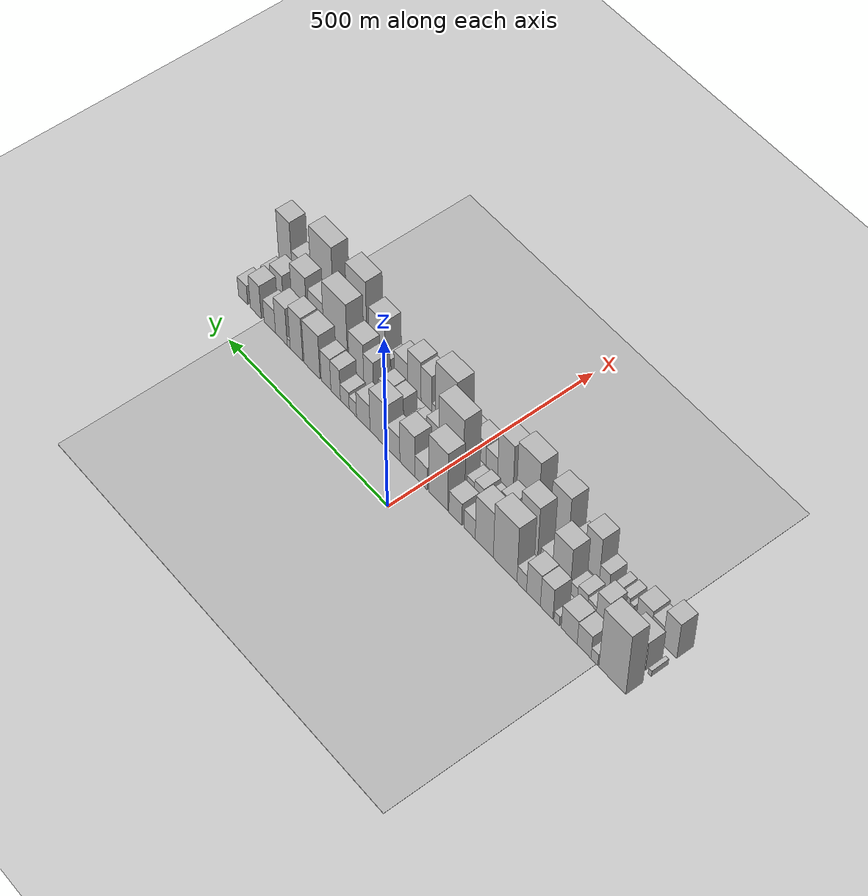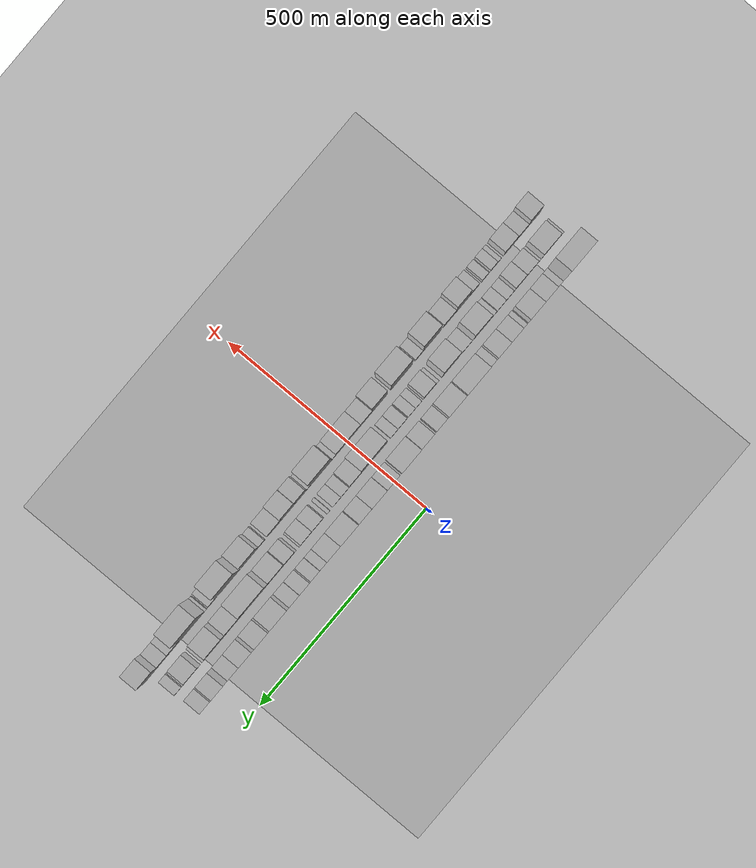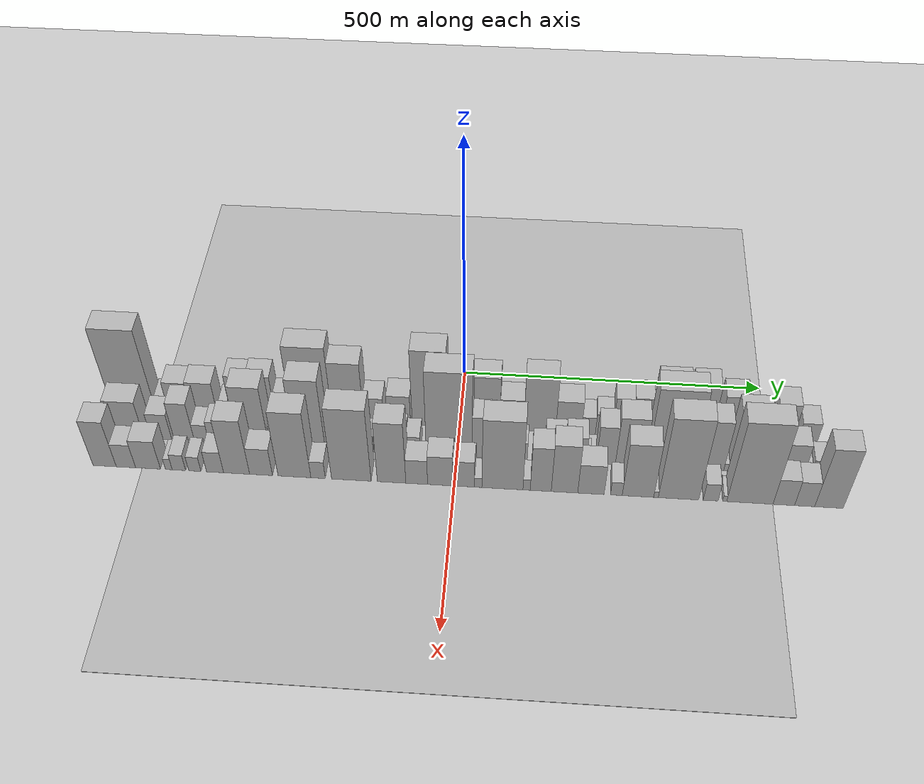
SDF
<?xml version="1.0" encoding="utf-8"?>

<sdf version="1.6">

   <world name="default">

      <gui fullscreen="0">

         <camera name="user_camera">

            <pose>-15 0 4.57585 0 0 0</pose>

            <view_controller>orbit</view_controller>

         </camera>

      </gui>

      <scene>

         <sky>

           <clouds>

             <speed>12</speed>

           </clouds>

         </sky>

         <ambient>0.4 0.4 0.4 1</ambient>

         <background>0.7 0.7 0.7 1</background>

         <shadows>1</shadows>

      </scene>

      <gravity>0 0 -9.8066</gravity>

      <magnetic_field>6e-06 2.3e-05 -4.2e-05</magnetic_field>

      <physics default="0" name="default_physics" type="ode">

         <ode>

            <solver>

               <type>quick</type>

               <iters>10</iters>

               <sor>1.0</sor>

               <use_dynamic_moi_rescaling>0</use_dynamic_moi_rescaling>

            </solver>

            <constraints>

               <cfm>0</cfm>

               <erp>0.2</erp>

               <contact_max_correcting_vel>100</contact_max_correcting_vel>

               <contact_surface_layer>0.001</contact_surface_layer>

            </constraints>

         </ode>

         <max_step_size>0.004</max_step_size>

         <real_time_factor>1</real_time_factor>

         <real_time_update_rate>250</real_time_update_rate>

      </physics>

      <light name="sun" type="directional">

         <cast_shadows>1</cast_shadows>

         <pose>0 0 10 0 0 0</pose>

         <diffuse>0.8 0.8 0.8 1</diffuse>

         <specular>0.2 0.2 0.2 1</specular>

         <attenuation>

            <range>1000</range>

            <constant>0.9</constant>

            <linear>0.01</linear>

            <quadratic>0.001</quadratic>

         </attenuation>

         <direction>-0.5 0.1 -0.9</direction>

      </light>

      <include>

         <name>ground_plane_1</name>

         <uri>model://HANNAS_ground_plane</uri>

         <pose>0 0 0  0 0 0</pose>

      </include>

      <include>

         <name>ground_plane_2</name>

         <uri>model://HANNAS_ground_plane</uri>

         <pose>100 0 0  0 0 0</pose>

      </include>

      <model name="building_1">

         <static>1</static>

         <pose frame="">100.0000 -543.3628 0 0.000000 0.000000 0.000000</pose>

         <link name="link">

            <pose frame="">0 0 96.00 0 0 0</pose>

            <collision name="collision">

               <geometry>

                  <box>

                     <size>40.0000 73.2743 192.0000</size>

                  </box>

               </geometry>

               <max_contacts>10</max_contacts>

               <surface>

                  <contact>

                     <ode/>

                  </contact>

                  <bounce/>

                  <friction>

                     <torsional>

                        <ode/>

                     </torsional>

                     <ode/>

                  </friction>

               </surface>

            </collision>

            <visual name="visual">

               <cast_shadows>0</cast_shadows>

               <geometry>

                  <box>

                     <size>40.0000 73.2743 192.0000</size>

                  </box>

               </geometry>

               <material>

                  <script>

                     <uri>model://HANNAS_wall/materials/scripts</uri>

                     <uri>model://HANNAS_wall/materials/textures</uri>

                     <name>vrc/HANNAS_wall</name>

                  </script>

               </material>

            </visual>

            <self_collide>0</self_collide>

            <enable_wind>0</enable_wind>

            <kinematic>0</kinematic>

         </link>

      </model>

      <model name="building_2">

         <static>1</static>

         <pose frame="">100.0000 -494.3452 0 0.000000 0.000000 0.000000</pose>

         <link name="link">

            <pose frame="">0 0 18.00 0 0 0</pose>

            <collision name="collision">

               <geometry>

                  <box>

                     <size>40.0000 18.7610 36.0000</size>

                  </box>

               </geometry>

               <max_contacts>10</max_contacts>

               <surface>

                  <contact>

                     <ode/>

                  </contact>

                  <bounce/>

                  <friction>

                     <torsional>

                        <ode/>

                     </torsional>

                     <ode/>

                  </friction>

               </surface>

            </collision>

            <visual name="visual">

               <cast_shadows>0</cast_shadows>

               <geometry>

                  <box>

                     <size>40.0000 18.7610 36.0000</size>

                  </box>

               </geometry>

               <material>

                  <script>

                     <uri>model://HANNAS_wall/materials/scripts</uri>

                     <uri>model://HANNAS_wall/materials/textures</uri>

                     <name>vrc/HANNAS_wall</name>

                  </script>

               </material>

            </visual>

            <self_collide>0</self_collide>

            <enable_wind>0</enable_wind>

            <kinematic>0</kinematic>

         </link>

      </model>

      <model name="building_3">

         <static>1</static>

         <pose frame="">100.0000 -466.0397 0 0.000000 0.000000 0.000000</pose>

         <link name="link">

            <pose frame="">0 0 36.00 0 0 0</pose>

            <collision name="collision">

               <geometry>

                  <box>

                     <size>40.0000 37.8501 72.0000</size>

                  </box>

               </geometry>

               <max_contacts>10</max_contacts>

               <surface>

                  <contact>

                     <ode/>

                  </contact>

                  <bounce/>

                  <friction>

                     <torsional>

                        <ode/>

                     </torsional>

                     <ode/>

                  </friction>

               </surface>

            </collision>

            <visual name="visual">

               <cast_shadows>0</cast_shadows>

               <geometry>

                  <box>

                     <size>40.0000 37.8501 72.0000</size>

                  </box>

               </geometry>

               <material>

                  <script>

                     <uri>model://HANNAS_wall/materials/scripts</uri>

                     <uri>model://HANNAS_wall/materials/textures</uri>

                     <name>vrc/HANNAS_wall</name>

                  </script>

               </material>

            </visual>

            <self_collide>0</self_collide>

            <enable_wind>0</enable_wind>

            <kinematic>0</kinematic>

         </link>

      </model>

      <model name="building_4">

         <static>1</static>

         <pose frame="">100.0000 -424.9990 0 0.000000 0.000000 0.000000</pose>

         <link name="link">

            <pose frame="">0 0 37.50 0 0 0</pose>

            <collision name="collision">

               <geometry>

                  <box>

                     <size>40.0000 44.2313 75.0000</size>

                  </box>

               </geometry>

               <max_contacts>10</max_contacts>

               <surface>

                  <contact>

                     <ode/>

                  </contact>

                  <bounce/>

                  <friction>

                     <torsional>

                        <ode/>

                     </torsional>

                     <ode/>

                  </friction>

               </surface>

            </collision>

            <visual name="visual">

               <cast_shadows>0</cast_shadows>

               <geometry>

                  <box>

                     <size>40.0000 44.2313 75.0000</size>

                  </box>

               </geometry>

               <material>

                  <script>

                     <uri>model://HANNAS_wall/materials/scripts</uri>

                     <uri>model://HANNAS_wall/materials/textures</uri>

                     <name>vrc/HANNAS_wall</name>

                  </script>

               </material>

            </visual>

            <self_collide>0</self_collide>

            <enable_wind>0</enable_wind>

            <kinematic>0</kinematic>

         </link>

      </model>

      <model name="building_5">

         <static>1</static>

         <pose frame="">100.0000 -390.2851 0 0.000000 0.000000 0.000000</pose>

         <link name="link">

            <pose frame="">0 0 15.00 0 0 0</pose>

            <collision name="collision">

               <geometry>

                  <box>

                     <size>40.0000 15.1964 30.0000</size>

                  </box>

               </geometry>

               <max_contacts>10</max_contacts>

               <surface>

                  <contact>

                     <ode/>

                  </contact>

                  <bounce/>

                  <friction>

                     <torsional>

                        <ode/>

                     </torsional>

                     <ode/>

                  </friction>

               </surface>

            </collision>

            <visual name="visual">

               <cast_shadows>0</cast_shadows>

               <geometry>

                  <box>

                     <size>40.0000 15.1964 30.0000</size>

                  </box>

               </geometry>

               <material>

                  <script>

                     <uri>model://HANNAS_wall/materials/scripts</uri>

                     <uri>model://HANNAS_wall/materials/textures</uri>

                     <name>vrc/HANNAS_wall</name>

                  </script>

               </material>

            </visual>

            <self_collide>0</self_collide>

            <enable_wind>0</enable_wind>

            <kinematic>0</kinematic>

         </link>

      </model>

      <model name="building_6">

         <static>1</static>

         <pose frame="">100.0000 -362.1027 0 0.000000 0.000000 0.000000</pose>

         <link name="link">

            <pose frame="">0 0 48.00 0 0 0</pose>

            <collision name="collision">

               <geometry>

                  <box>

                     <size>40.0000 35.1683 96.0000</size>

                  </box>

               </geometry>

               <max_contacts>10</max_contacts>

               <surface>

                  <contact>

                     <ode/>

                  </contact>

                  <bounce/>

                  <friction>

                     <torsional>

                        <ode/>

                     </torsional>

                     <ode/>

                  </friction>

               </surface>

            </collision>

            <visual name="visual">

               <cast_shadows>0</cast_shadows>

               <geometry>

                  <box>

                     <size>40.0000 35.1683 96.0000</size>

                  </box>

               </geometry>

               <material>

                  <script>

                     <uri>model://HANNAS_wall/materials/scripts</uri>

                     <uri>model://HANNAS_wall/materials/textures</uri>

                     <name>vrc/HANNAS_wall</name>

                  </script>

               </material>

            </visual>

            <self_collide>0</self_collide>

            <enable_wind>0</enable_wind>

            <kinematic>0</kinematic>

         </link>

      </model>

      <model name="building_7">

         <static>1</static>

         <pose frame="">100.0000 -324.9261 0 0.000000 0.000000 0.000000</pose>

         <link name="link">

            <pose frame="">0 0 49.50 0 0 0</pose>

            <collision name="collision">

               <geometry>

                  <box>

                     <size>40.0000 39.1849 99.0000</size>

                  </box>

               </geometry>

               <max_contacts>10</max_contacts>

               <surface>

                  <contact>

                     <ode/>

                  </contact>

                  <bounce/>

                  <friction>

                     <torsional>

                        <ode/>

                     </torsional>

                     <ode/>

                  </friction>

               </surface>

            </collision>

            <visual name="visual">

               <cast_shadows>0</cast_shadows>

               <geometry>

                  <box>

                     <size>40.0000 39.1849 99.0000</size>

                  </box>

               </geometry>

               <material>

                  <script>

                     <uri>model://HANNAS_wall/materials/scripts</uri>

                     <uri>model://HANNAS_wall/materials/textures</uri>

                     <name>vrc/HANNAS_wall</name>

                  </script>

               </material>

            </visual>

            <self_collide>0</self_collide>

            <enable_wind>0</enable_wind>

            <kinematic>0</kinematic>

         </link>

      </model>

      <model name="building_8">

         <static>1</static>

         <pose frame="">100.0000 -291.7243 0 0.000000 0.000000 0.000000</pose>

         <link name="link">

            <pose frame="">0 0 27.00 0 0 0</pose>

            <collision name="collision">

               <geometry>

                  <box>

                     <size>40.0000 27.2187 54.0000</size>

                  </box>

               </geometry>

               <max_contacts>10</max_contacts>

               <surface>

                  <contact>

                     <ode/>

                  </contact>

                  <bounce/>

                  <friction>

                     <torsional>

                        <ode/>

                     </torsional>

                     <ode/>

                  </friction>

               </surface>

            </collision>

            <visual name="visual">

               <cast_shadows>0</cast_shadows>

               <geometry>

                  <box>

                     <size>40.0000 27.2187 54.0000</size>

                  </box>

               </geometry>

               <material>

                  <script>

                     <uri>model://HANNAS_wall/materials/scripts</uri>

                     <uri>model://HANNAS_wall/materials/textures</uri>

                     <name>vrc/HANNAS_wall</name>

                  </script>

               </material>

            </visual>

            <self_collide>0</self_collide>

            <enable_wind>0</enable_wind>

            <kinematic>0</kinematic>

         </link>

      </model>

      <model name="building_9">

         <static>1</static>

         <pose frame="">100.0000 -244.1789 0 0.000000 0.000000 0.000000</pose>

         <link name="link">

            <pose frame="">0 0 87.00 0 0 0</pose>

            <collision name="collision">

               <geometry>

                  <box>

                     <size>40.0000 67.8723 174.0000</size>

                  </box>

               </geometry>

               <max_contacts>10</max_contacts>

               <surface>

                  <contact>

                     <ode/>

                  </contact>

                  <bounce/>

                  <friction>

                     <torsional>

                        <ode/>

                     </torsional>

                     <ode/>

                  </friction>

               </surface>

            </collision>

            <visual name="visual">

               <cast_shadows>0</cast_shadows>

               <geometry>

                  <box>

                     <size>40.0000 67.8723 174.0000</size>

                  </box>

               </geometry>

               <material>

                  <script>

                     <uri>model://HANNAS_wall/materials/scripts</uri>

                     <uri>model://HANNAS_wall/materials/textures</uri>

                     <name>vrc/HANNAS_wall</name>

                  </script>

               </material>

            </visual>

            <self_collide>0</self_collide>

            <enable_wind>0</enable_wind>

            <kinematic>0</kinematic>

         </link>

      </model>

      <model name="building_10">

         <static>1</static>

         <pose frame="">100.0000 -184.0517 0 0.000000 0.000000 0.000000</pose>

         <link name="link">

            <pose frame="">0 0 70.50 0 0 0</pose>

            <collision name="collision">

               <geometry>

                  <box>

                     <size>40.0000 52.3820 141.0000</size>

                  </box>

               </geometry>

               <max_contacts>10</max_contacts>

               <surface>

                  <contact>

                     <ode/>

                  </contact>

                  <bounce/>

                  <friction>

                     <torsional>

                        <ode/>

                     </torsional>

                     <ode/>

                  </friction>

               </surface>

            </collision>

            <visual name="visual">

               <cast_shadows>0</cast_shadows>

               <geometry>

                  <box>

                     <size>40.0000 52.3820 141.0000</size>

                  </box>

               </geometry>

               <material>

                  <script>

                     <uri>model://HANNAS_wall/materials/scripts</uri>

                     <uri>model://HANNAS_wall/materials/textures</uri>

                     <name>vrc/HANNAS_wall</name>

                  </script>

               </material>

            </visual>

            <self_collide>0</self_collide>

            <enable_wind>0</enable_wind>

            <kinematic>0</kinematic>

         </link>

      </model>

      <model name="building_11">

         <static>1</static>

         <pose frame="">100.0000 -141.3786 0 0.000000 0.000000 0.000000</pose>

         <link name="link">

            <pose frame="">0 0 30.00 0 0 0</pose>

            <collision name="collision">

               <geometry>

                  <box>

                     <size>40.0000 32.9641 60.0000</size>

                  </box>

               </geometry>

               <max_contacts>10</max_contacts>

               <surface>

                  <contact>

                     <ode/>

                  </contact>

                  <bounce/>

                  <friction>

                     <torsional>

                        <ode/>

                     </torsional>

                     <ode/>

                  </friction>

               </surface>

            </collision>

            <visual name="visual">

               <cast_shadows>0</cast_shadows>

               <geometry>

                  <box>

                     <size>40.0000 32.9641 60.0000</size>

                  </box>

               </geometry>

               <material>

                  <script>

                     <uri>model://HANNAS_wall/materials/scripts</uri>

                     <uri>model://HANNAS_wall/materials/textures</uri>

                     <name>vrc/HANNAS_wall</name>

                  </script>

               </material>

            </visual>

            <self_collide>0</self_collide>

            <enable_wind>0</enable_wind>

            <kinematic>0</kinematic>

         </link>

      </model>

      <model name="building_12">

         <static>1</static>

         <pose frame="">100.0000 -99.7368 0 0.000000 0.000000 0.000000</pose>

         <link name="link">

            <pose frame="">0 0 34.50 0 0 0</pose>

            <collision name="collision">

               <geometry>

                  <box>

                     <size>40.0000 38.3196 69.0000</size>

                  </box>

               </geometry>

               <max_contacts>10</max_contacts>

               <surface>

                  <contact>

                     <ode/>

                  </contact>

                  <bounce/>

                  <friction>

                     <torsional>

                        <ode/>

                     </torsional>

                     <ode/>

                  </friction>

               </surface>

            </collision>

            <visual name="visual">

               <cast_shadows>0</cast_shadows>

               <geometry>

                  <box>

                     <size>40.0000 38.3196 69.0000</size>

                  </box>

               </geometry>

               <material>

                  <script>

                     <uri>model://HANNAS_wall/materials/scripts</uri>

                     <uri>model://HANNAS_wall/materials/textures</uri>

                     <name>vrc/HANNAS_wall</name>

                  </script>

               </material>

            </visual>

            <self_collide>0</self_collide>

            <enable_wind>0</enable_wind>

            <kinematic>0</kinematic>

         </link>

      </model>

      <model name="building_13">

         <static>1</static>

         <pose frame="">100.0000 -49.0089 0 0.000000 0.000000 0.000000</pose>

         <link name="link">

            <pose frame="">0 0 90.00 0 0 0</pose>

            <collision name="collision">

               <geometry>

                  <box>

                     <size>40.0000 57.1362 180.0000</size>

                  </box>

               </geometry>

               <max_contacts>10</max_contacts>

               <surface>

                  <contact>

                     <ode/>

                  </contact>

                  <bounce/>

                  <friction>

                     <torsional>

                        <ode/>

                     </torsional>

                     <ode/>

                  </friction>

               </surface>

            </collision>

            <visual name="visual">

               <cast_shadows>0</cast_shadows>

               <geometry>

                  <box>

                     <size>40.0000 57.1362 180.0000</size>

                  </box>

               </geometry>

               <material>

                  <script>

                     <uri>model://HANNAS_wall/materials/scripts</uri>

                     <uri>model://HANNAS_wall/materials/textures</uri>

                     <name>vrc/HANNAS_wall</name>

                  </script>

               </material>

            </visual>

            <self_collide>0</self_collide>

            <enable_wind>0</enable_wind>

            <kinematic>0</kinematic>

         </link>

      </model>

      <model name="building_14">

         <static>1</static>

         <pose frame="">100.0000 2.4698 0 0.000000 0.000000 0.000000</pose>

         <link name="link">

            <pose frame="">0 0 34.50 0 0 0</pose>

            <collision name="collision">

               <geometry>

                  <box>

                     <size>40.0000 37.8213 69.0000</size>

                  </box>

               </geometry>

               <max_contacts>10</max_contacts>

               <surface>

                  <contact>

                     <ode/>

                  </contact>

                  <bounce/>

                  <friction>

                     <torsional>

                        <ode/>

                     </torsional>

                     <ode/>

                  </friction>

               </surface>

            </collision>

            <visual name="visual">

               <cast_shadows>0</cast_shadows>

               <geometry>

                  <box>

                     <size>40.0000 37.8213 69.0000</size>

                  </box>

               </geometry>

               <material>

                  <script>

                     <uri>model://HANNAS_wall/materials/scripts</uri>

                     <uri>model://HANNAS_wall/materials/textures</uri>

                     <name>vrc/HANNAS_wall</name>

                  </script>

               </material>

            </visual>

            <self_collide>0</self_collide>

            <enable_wind>0</enable_wind>

            <kinematic>0</kinematic>

         </link>

      </model>

      <model name="building_15">

         <static>1</static>

         <pose frame="">100.0000 43.9420 0 0.000000 0.000000 0.000000</pose>

         <link name="link">

            <pose frame="">0 0 63.00 0 0 0</pose>

            <collision name="collision">

               <geometry>

                  <box>

                     <size>40.0000 45.1230 126.0000</size>

                  </box>

               </geometry>

               <max_contacts>10</max_contacts>

               <surface>

                  <contact>

                     <ode/>

                  </contact>

                  <bounce/>

                  <friction>

                     <torsional>

                        <ode/>

                     </torsional>

                     <ode/>

                  </friction>

               </surface>

            </collision>

            <visual name="visual">

               <cast_shadows>0</cast_shadows>

               <geometry>

                  <box>

                     <size>40.0000 45.1230 126.0000</size>

                  </box>

               </geometry>

               <material>

                  <script>

                     <uri>model://HANNAS_wall/materials/scripts</uri>

                     <uri>model://HANNAS_wall/materials/textures</uri>

                     <name>vrc/HANNAS_wall</name>

                  </script>

               </material>

            </visual>

            <self_collide>0</self_collide>

            <enable_wind>0</enable_wind>

            <kinematic>0</kinematic>

         </link>

      </model>

      <model name="building_16">

         <static>1</static>

         <pose frame="">100.0000 85.9901 0 0.000000 0.000000 0.000000</pose>

         <link name="link">

            <pose frame="">0 0 37.50 0 0 0</pose>

            <collision name="collision">

               <geometry>

                  <box>

                     <size>40.0000 38.9731 75.0000</size>

                  </box>

               </geometry>

               <max_contacts>10</max_contacts>

               <surface>

                  <contact>

                     <ode/>

                  </contact>

                  <bounce/>

                  <friction>

                     <torsional>

                        <ode/>

                     </torsional>

                     <ode/>

                  </friction>

               </surface>

            </collision>

            <visual name="visual">

               <cast_shadows>0</cast_shadows>

               <geometry>

                  <box>

                     <size>40.0000 38.9731 75.0000</size>

                  </box>

               </geometry>

               <material>

                  <script>

                     <uri>model://HANNAS_wall/materials/scripts</uri>

                     <uri>model://HANNAS_wall/materials/textures</uri>

                     <name>vrc/HANNAS_wall</name>

                  </script>

               </material>

            </visual>

            <self_collide>0</self_collide>

            <enable_wind>0</enable_wind>

            <kinematic>0</kinematic>

         </link>

      </model>

      <model name="building_17">

         <static>1</static>

         <pose frame="">100.0000 131.7560 0 0.000000 0.000000 0.000000</pose>

         <link name="link">

            <pose frame="">0 0 66.00 0 0 0</pose>

            <collision name="collision">

               <geometry>

                  <box>

                     <size>40.0000 52.5588 132.0000</size>

                  </box>

               </geometry>

               <max_contacts>10</max_contacts>

               <surface>

                  <contact>

                     <ode/>

                  </contact>

                  <bounce/>

                  <friction>

                     <torsional>

                        <ode/>

                     </torsional>

                     <ode/>

                  </friction>

               </surface>

            </collision>

            <visual name="visual">

               <cast_shadows>0</cast_shadows>

               <geometry>

                  <box>

                     <size>40.0000 52.5588 132.0000</size>

                  </box>

               </geometry>

               <material>

                  <script>

                     <uri>model://HANNAS_wall/materials/scripts</uri>

                     <uri>model://HANNAS_wall/materials/textures</uri>

                     <name>vrc/HANNAS_wall</name>

                  </script>

               </material>

            </visual>

            <self_collide>0</self_collide>

            <enable_wind>0</enable_wind>

            <kinematic>0</kinematic>

         </link>

      </model>

      <model name="building_18">

         <static>1</static>

         <pose frame="">100.0000 179.0775 0 0.000000 0.000000 0.000000</pose>

         <link name="link">

            <pose frame="">0 0 39.00 0 0 0</pose>

            <collision name="collision">

               <geometry>

                  <box>

                     <size>40.0000 42.0843 78.0000</size>

                  </box>

               </geometry>

               <max_contacts>10</max_contacts>

               <surface>

                  <contact>

                     <ode/>

                  </contact>

                  <bounce/>

                  <friction>

                     <torsional>

                        <ode/>

                     </torsional>

                     <ode/>

                  </friction>

               </surface>

            </collision>

            <visual name="visual">

               <cast_shadows>0</cast_shadows>

               <geometry>

                  <box>

                     <size>40.0000 42.0843 78.0000</size>

                  </box>

               </geometry>

               <material>

                  <script>

                     <uri>model://HANNAS_wall/materials/scripts</uri>

                     <uri>model://HANNAS_wall/materials/textures</uri>

                     <name>vrc/HANNAS_wall</name>

                  </script>

               </material>

            </visual>

            <self_collide>0</self_collide>

            <enable_wind>0</enable_wind>

            <kinematic>0</kinematic>

         </link>

      </model>

      <model name="building_19">

         <static>1</static>

         <pose frame="">100.0000 211.5534 0 0.000000 0.000000 0.000000</pose>

         <link name="link">

            <pose frame="">0 0 21.00 0 0 0</pose>

            <collision name="collision">

               <geometry>

                  <box>

                     <size>40.0000 22.8676 42.0000</size>

                  </box>

               </geometry>

               <max_contacts>10</max_contacts>

               <surface>

                  <contact>

                     <ode/>

                  </contact>

                  <bounce/>

                  <friction>

                     <torsional>

                        <ode/>

                     </torsional>

                     <ode/>

                  </friction>

               </surface>

            </collision>

            <visual name="visual">

               <cast_shadows>0</cast_shadows>

               <geometry>

                  <box>

                     <size>40.0000 22.8676 42.0000</size>

                  </box>

               </geometry>

               <material>

                  <script>

                     <uri>model://HANNAS_wall/materials/scripts</uri>

                     <uri>model://HANNAS_wall/materials/textures</uri>

                     <name>vrc/HANNAS_wall</name>

                  </script>

               </material>

            </visual>

            <self_collide>0</self_collide>

            <enable_wind>0</enable_wind>

            <kinematic>0</kinematic>

         </link>

      </model>

      <model name="building_20">

         <static>1</static>

         <pose frame="">100.0000 236.6745 0 0.000000 0.000000 0.000000</pose>

         <link name="link">

            <pose frame="">0 0 25.50 0 0 0</pose>

            <collision name="collision">

               <geometry>

                  <box>

                     <size>40.0000 27.3745 51.0000</size>

                  </box>

               </geometry>

               <max_contacts>10</max_contacts>

               <surface>

                  <contact>

                     <ode/>

                  </contact>

                  <bounce/>

                  <friction>

                     <torsional>

                        <ode/>

                     </torsional>

                     <ode/>

                  </friction>

               </surface>

            </collision>

            <visual name="visual">

               <cast_shadows>0</cast_shadows>

               <geometry>

                  <box>

                     <size>40.0000 27.3745 51.0000</size>

                  </box>

               </geometry>

               <material>

                  <script>

                     <uri>model://HANNAS_wall/materials/scripts</uri>

                     <uri>model://HANNAS_wall/materials/textures</uri>

                     <name>vrc/HANNAS_wall</name>

                  </script>

               </material>

            </visual>

            <self_collide>0</self_collide>

            <enable_wind>0</enable_wind>

            <kinematic>0</kinematic>

         </link>

      </model>

      <model name="building_21">

         <static>1</static>

         <pose frame="">100.0000 265.3255 0 0.000000 0.000000 0.000000</pose>

         <link name="link">

            <pose frame="">0 0 46.50 0 0 0</pose>

            <collision name="collision">

               <geometry>

                  <box>

                     <size>40.0000 29.9275 93.0000</size>

                  </box>

               </geometry>

               <max_contacts>10</max_contacts>

               <surface>

                  <contact>

                     <ode/>

                  </contact>

                  <bounce/>

                  <friction>

                     <torsional>

                        <ode/>

                     </torsional>

                     <ode/>

                  </friction>

               </surface>

            </collision>

            <visual name="visual">

               <cast_shadows>0</cast_shadows>

               <geometry>

                  <box>

                     <size>40.0000 29.9275 93.0000</size>

                  </box>

               </geometry>

               <material>

                  <script>

                     <uri>model://HANNAS_wall/materials/scripts</uri>

                     <uri>model://HANNAS_wall/materials/textures</uri>

                     <name>vrc/HANNAS_wall</name>

                  </script>

               </material>

            </visual>

            <self_collide>0</self_collide>

            <enable_wind>0</enable_wind>

            <kinematic>0</kinematic>

         </link>

      </model>

      <model name="building_22">

         <static>1</static>

         <pose frame="">100.0000 295.5824 0 0.000000 0.000000 0.000000</pose>

         <link name="link">

            <pose frame="">0 0 48.00 0 0 0</pose>

            <collision name="collision">

               <geometry>

                  <box>

                     <size>40.0000 30.5863 96.0000</size>

                  </box>

               </geometry>

               <max_contacts>10</max_contacts>

               <surface>

                  <contact>

                     <ode/>

                  </contact>

                  <bounce/>

                  <friction>

                     <torsional>

                        <ode/>

                     </torsional>

                     <ode/>

                  </friction>

               </surface>

            </collision>

            <visual name="visual">

               <cast_shadows>0</cast_shadows>

               <geometry>

                  <box>

                     <size>40.0000 30.5863 96.0000</size>

                  </box>

               </geometry>

               <material>

                  <script>

                     <uri>model://HANNAS_wall/materials/scripts</uri>

                     <uri>model://HANNAS_wall/materials/textures</uri>

                     <name>vrc/HANNAS_wall</name>

                  </script>

               </material>

            </visual>

            <self_collide>0</self_collide>

            <enable_wind>0</enable_wind>

            <kinematic>0</kinematic>

         </link>

      </model>

      <model name="building_23">

         <static>1</static>

         <pose frame="">100.0000 340.3193 0 0.000000 0.000000 0.000000</pose>

         <link name="link">

            <pose frame="">0 0 66.00 0 0 0</pose>

            <collision name="collision">

               <geometry>

                  <box>

                     <size>40.0000 50.8875 132.0000</size>

                  </box>

               </geometry>

               <max_contacts>10</max_contacts>

               <surface>

                  <contact>

                     <ode/>

                  </contact>

                  <bounce/>

                  <friction>

                     <torsional>

                        <ode/>

                     </torsional>

                     <ode/>

                  </friction>

               </surface>

            </collision>

            <visual name="visual">

               <cast_shadows>0</cast_shadows>

               <geometry>

                  <box>

                     <size>40.0000 50.8875 132.0000</size>

                  </box>

               </geometry>

               <material>

                  <script>

                     <uri>model://HANNAS_wall/materials/scripts</uri>

                     <uri>model://HANNAS_wall/materials/textures</uri>

                     <name>vrc/HANNAS_wall</name>

                  </script>

               </material>

            </visual>

            <self_collide>0</self_collide>

            <enable_wind>0</enable_wind>

            <kinematic>0</kinematic>

         </link>

      </model>

      <model name="building_24">

         <static>1</static>

         <pose frame="">100.0000 390.0268 0 0.000000 0.000000 0.000000</pose>

         <link name="link">

            <pose frame="">0 0 66.00 0 0 0</pose>

            <collision name="collision">

               <geometry>

                  <box>

                     <size>40.0000 40.5276 132.0000</size>

                  </box>

               </geometry>

               <max_contacts>10</max_contacts>

               <surface>

                  <contact>

                     <ode/>

                  </contact>

                  <bounce/>

                  <friction>

                     <torsional>

                        <ode/>

                     </torsional>

                     <ode/>

                  </friction>

               </surface>

            </collision>

            <visual name="visual">

               <cast_shadows>0</cast_shadows>

               <geometry>

                  <box>

                     <size>40.0000 40.5276 132.0000</size>

                  </box>

               </geometry>

               <material>

                  <script>

                     <uri>model://HANNAS_wall/materials/scripts</uri>

                     <uri>model://HANNAS_wall/materials/textures</uri>

                     <name>vrc/HANNAS_wall</name>

                  </script>

               </material>

            </visual>

            <self_collide>0</self_collide>

            <enable_wind>0</enable_wind>

            <kinematic>0</kinematic>

         </link>

      </model>

      <model name="building_25">

         <static>1</static>

         <pose frame="">100.0000 415.1242 0 0.000000 0.000000 0.000000</pose>

         <link name="link">

            <pose frame="">0 0 12.00 0 0 0</pose>

            <collision name="collision">

               <geometry>

                  <box>

                     <size>40.0000 9.6672 24.0000</size>

                  </box>

               </geometry>

               <max_contacts>10</max_contacts>

               <surface>

                  <contact>

                     <ode/>

                  </contact>

                  <bounce/>

                  <friction>

                     <torsional>

                        <ode/>

                     </torsional>

                     <ode/>

                  </friction>

               </surface>

            </collision>

            <visual name="visual">

               <cast_shadows>0</cast_shadows>

               <geometry>

                  <box>

                     <size>40.0000 9.6672 24.0000</size>

                  </box>

               </geometry>

               <material>

                  <script>

                     <uri>model://HANNAS_wall/materials/scripts</uri>

                     <uri>model://HANNAS_wall/materials/textures</uri>

                     <name>vrc/HANNAS_wall</name>

                  </script>

               </material>

            </visual>

            <self_collide>0</self_collide>

            <enable_wind>0</enable_wind>

            <kinematic>0</kinematic>

         </link>

      </model>

      <model name="building_26">

         <static>1</static>

         <pose frame="">100.0000 438.9646 0 0.000000 0.000000 0.000000</pose>

         <link name="link">

            <pose frame="">0 0 55.50 0 0 0</pose>

            <collision name="collision">

               <geometry>

                  <box>

                     <size>40.0000 38.0136 111.0000</size>

                  </box>

               </geometry>

               <max_contacts>10</max_contacts>

               <surface>

                  <contact>

                     <ode/>

                  </contact>

                  <bounce/>

                  <friction>

                     <torsional>

                        <ode/>

                     </torsional>

                     <ode/>

                  </friction>

               </surface>

            </collision>

            <visual name="visual">

               <cast_shadows>0</cast_shadows>

               <geometry>

                  <box>

                     <size>40.0000 38.0136 111.0000</size>

                  </box>

               </geometry>

               <material>

                  <script>

                     <uri>model://HANNAS_wall/materials/scripts</uri>

                     <uri>model://HANNAS_wall/materials/textures</uri>

                     <name>vrc/HANNAS_wall</name>

                  </script>

               </material>

            </visual>

            <self_collide>0</self_collide>

            <enable_wind>0</enable_wind>

            <kinematic>0</kinematic>

         </link>

      </model>

      <model name="building_27">

         <static>1</static>

         <pose frame="">100.0000 476.7719 0 0.000000 0.000000 0.000000</pose>

         <link name="link">

            <pose frame="">0 0 34.50 0 0 0</pose>

            <collision name="collision">

               <geometry>

                  <box>

                     <size>40.0000 37.6010 69.0000</size>

                  </box>

               </geometry>

               <max_contacts>10</max_contacts>

               <surface>

                  <contact>

                     <ode/>

                  </contact>

                  <bounce/>

                  <friction>

                     <torsional>

                        <ode/>

                     </torsional>

                     <ode/>

                  </friction>

               </surface>

            </collision>

            <visual name="visual">

               <cast_shadows>0</cast_shadows>

               <geometry>

                  <box>

                     <size>40.0000 37.6010 69.0000</size>

                  </box>

               </geometry>

               <material>

                  <script>

                     <uri>model://HANNAS_wall/materials/scripts</uri>

                     <uri>model://HANNAS_wall/materials/textures</uri>

                     <name>vrc/HANNAS_wall</name>

                  </script>

               </material>

            </visual>

            <self_collide>0</self_collide>

            <enable_wind>0</enable_wind>

            <kinematic>0</kinematic>

         </link>

      </model>

      <model name="building_28">

         <static>1</static>

         <pose frame="">100.0000 522.5109 0 0.000000 0.000000 0.000000</pose>

         <link name="link">

            <pose frame="">0 0 49.50 0 0 0</pose>

            <collision name="collision">

               <geometry>

                  <box>

                     <size>40.0000 35.8769 99.0000</size>

                  </box>

               </geometry>

               <max_contacts>10</max_contacts>

               <surface>

                  <contact>

                     <ode/>

                  </contact>

                  <bounce/>

                  <friction>

                     <torsional>

                        <ode/>

                     </torsional>

                     <ode/>

                  </friction>

               </surface>

            </collision>

            <visual name="visual">

               <cast_shadows>0</cast_shadows>

               <geometry>

                  <box>

                     <size>40.0000 35.8769 99.0000</size>

                  </box>

               </geometry>

               <material>

                  <script>

                     <uri>model://HANNAS_wall/materials/scripts</uri>

                     <uri>model://HANNAS_wall/materials/textures</uri>

                     <name>vrc/HANNAS_wall</name>

                  </script>

               </material>

            </visual>

            <self_collide>0</self_collide>

            <enable_wind>0</enable_wind>

            <kinematic>0</kinematic>

         </link>

      </model>

      <model name="building_29">

         <static>1</static>

         <pose frame="">100.0000 564.7306 0 0.000000 0.000000 0.000000</pose>

         <link name="link">

            <pose frame="">0 0 28.50 0 0 0</pose>

            <collision name="collision">

               <geometry>

                  <box>

                     <size>40.0000 30.5626 57.0000</size>

                  </box>

               </geometry>

               <max_contacts>10</max_contacts>

               <surface>

                  <contact>

                     <ode/>

                  </contact>

                  <bounce/>

                  <friction>

                     <torsional>

                        <ode/>

                     </torsional>

                     <ode/>

                  </friction>

               </surface>

            </collision>

            <visual name="visual">

               <cast_shadows>0</cast_shadows>

               <geometry>

                  <box>

                     <size>40.0000 30.5626 57.0000</size>

                  </box>

               </geometry>

               <material>

                  <script>

                     <uri>model://HANNAS_wall/materials/scripts</uri>

                     <uri>model://HANNAS_wall/materials/textures</uri>

                     <name>vrc/HANNAS_wall</name>

                  </script>

               </material>

            </visual>

            <self_collide>0</self_collide>

            <enable_wind>0</enable_wind>

            <kinematic>0</kinematic>

         </link>

      </model>

      <model name="building_30">

         <static>1</static>

         <pose frame="">160.0000 -575.5376 0 0.000000 0.000000 0.000000</pose>

         <link name="link">

            <pose frame="">0 0 9.00 0 0 0</pose>

            <collision name="collision">

               <geometry>

                  <box>

                     <size>40.0000 8.9249 18.0000</size>

                  </box>

               </geometry>

               <max_contacts>10</max_contacts>

               <surface>

                  <contact>

                     <ode/>

                  </contact>

                  <bounce/>

                  <friction>

                     <torsional>

                        <ode/>

                     </torsional>

                     <ode/>

                  </friction>

               </surface>

            </collision>

            <visual name="visual">

               <cast_shadows>0</cast_shadows>

               <geometry>

                  <box>

                     <size>40.0000 8.9249 18.0000</size>

                  </box>

               </geometry>

               <material>

                  <script>

                     <uri>model://HANNAS_wall/materials/scripts</uri>

                     <uri>model://HANNAS_wall/materials/textures</uri>

                     <name>vrc/HANNAS_wall</name>

                  </script>

               </material>

            </visual>

            <self_collide>0</self_collide>

            <enable_wind>0</enable_wind>

            <kinematic>0</kinematic>

         </link>

      </model>

      <model name="building_31">

         <static>1</static>

         <pose frame="">160.0000 -537.7754 0 0.000000 0.000000 0.000000</pose>

         <link name="link">

            <pose frame="">0 0 45.00 0 0 0</pose>

            <collision name="collision">

               <geometry>

                  <box>

                     <size>40.0000 52.5994 90.0000</size>

                  </box>

               </geometry>

               <max_contacts>10</max_contacts>

               <surface>

                  <contact>

                     <ode/>

                  </contact>

                  <bounce/>

                  <friction>

                     <torsional>

                        <ode/>

                     </torsional>

                     <ode/>

                  </friction>

               </surface>

            </collision>

            <visual name="visual">

               <cast_shadows>0</cast_shadows>

               <geometry>

                  <box>

                     <size>40.0000 52.5994 90.0000</size>

                  </box>

               </geometry>

               <material>

                  <script>

                     <uri>model://HANNAS_wall/materials/scripts</uri>

                     <uri>model://HANNAS_wall/materials/textures</uri>

                     <name>vrc/HANNAS_wall</name>

                  </script>

               </material>

            </visual>

            <self_collide>0</self_collide>

            <enable_wind>0</enable_wind>

            <kinematic>0</kinematic>

         </link>

      </model>

      <model name="building_32">

         <static>1</static>

         <pose frame="">160.0000 -507.9673 0 0.000000 0.000000 0.000000</pose>

         <link name="link">

            <pose frame="">0 0 7.50 0 0 0</pose>

            <collision name="collision">

               <geometry>

                  <box>

                     <size>40.0000 7.0168 15.0000</size>

                  </box>

               </geometry>

               <max_contacts>10</max_contacts>

               <surface>

                  <contact>

                     <ode/>

                  </contact>

                  <bounce/>

                  <friction>

                     <torsional>

                        <ode/>

                     </torsional>

                     <ode/>

                  </friction>

               </surface>

            </collision>

            <visual name="visual">

               <cast_shadows>0</cast_shadows>

               <geometry>

                  <box>

                     <size>40.0000 7.0168 15.0000</size>

                  </box>

               </geometry>

               <material>

                  <script>

                     <uri>model://HANNAS_wall/materials/scripts</uri>

                     <uri>model://HANNAS_wall/materials/textures</uri>

                     <name>vrc/HANNAS_wall</name>

                  </script>

               </material>

            </visual>

            <self_collide>0</self_collide>

            <enable_wind>0</enable_wind>

            <kinematic>0</kinematic>

         </link>

      </model>

      <model name="building_33">

         <static>1</static>

         <pose frame="">160.0000 -482.4721 0 0.000000 0.000000 0.000000</pose>

         <link name="link">

            <pose frame="">0 0 31.50 0 0 0</pose>

            <collision name="collision">

               <geometry>

                  <box>

                     <size>40.0000 33.9736 63.0000</size>

                  </box>

               </geometry>

               <max_contacts>10</max_contacts>

               <surface>

                  <contact>

                     <ode/>

                  </contact>

                  <bounce/>

                  <friction>

                     <torsional>

                        <ode/>

                     </torsional>

                     <ode/>

                  </friction>

               </surface>

            </collision>

            <visual name="visual">

               <cast_shadows>0</cast_shadows>

               <geometry>

                  <box>

                     <size>40.0000 33.9736 63.0000</size>

                  </box>

               </geometry>

               <material>

                  <script>

                     <uri>model://HANNAS_wall/materials/scripts</uri>

                     <uri>model://HANNAS_wall/materials/textures</uri>

                     <name>vrc/HANNAS_wall</name>

                  </script>

               </material>

            </visual>

            <self_collide>0</self_collide>

            <enable_wind>0</enable_wind>

            <kinematic>0</kinematic>

         </link>

      </model>

      <model name="building_34">

         <static>1</static>

         <pose frame="">160.0000 -444.8592 0 0.000000 0.000000 0.000000</pose>

         <link name="link">

            <pose frame="">0 0 46.50 0 0 0</pose>

            <collision name="collision">

               <geometry>

                  <box>

                     <size>40.0000 33.2523 93.0000</size>

                  </box>

               </geometry>

               <max_contacts>10</max_contacts>

               <surface>

                  <contact>

                     <ode/>

                  </contact>

                  <bounce/>

                  <friction>

                     <torsional>

                        <ode/>

                     </torsional>

                     <ode/>

                  </friction>

               </surface>

            </collision>

            <visual name="visual">

               <cast_shadows>0</cast_shadows>

               <geometry>

                  <box>

                     <size>40.0000 33.2523 93.0000</size>

                  </box>

               </geometry>

               <material>

                  <script>

                     <uri>model://HANNAS_wall/materials/scripts</uri>

                     <uri>model://HANNAS_wall/materials/textures</uri>

                     <name>vrc/HANNAS_wall</name>

                  </script>

               </material>

            </visual>

            <self_collide>0</self_collide>

            <enable_wind>0</enable_wind>

            <kinematic>0</kinematic>

         </link>

      </model>

      <model name="building_35">

         <static>1</static>

         <pose frame="">160.0000 -416.3268 0 0.000000 0.000000 0.000000</pose>

         <link name="link">

            <pose frame="">0 0 21.00 0 0 0</pose>

            <collision name="collision">

               <geometry>

                  <box>

                     <size>40.0000 23.8125 42.0000</size>

                  </box>

               </geometry>

               <max_contacts>10</max_contacts>

               <surface>

                  <contact>

                     <ode/>

                  </contact>

                  <bounce/>

                  <friction>

                     <torsional>

                        <ode/>

                     </torsional>

                     <ode/>

                  </friction>

               </surface>

            </collision>

            <visual name="visual">

               <cast_shadows>0</cast_shadows>

               <geometry>

                  <box>

                     <size>40.0000 23.8125 42.0000</size>

                  </box>

               </geometry>

               <material>

                  <script>

                     <uri>model://HANNAS_wall/materials/scripts</uri>

                     <uri>model://HANNAS_wall/materials/textures</uri>

                     <name>vrc/HANNAS_wall</name>

                  </script>

               </material>

            </visual>

            <self_collide>0</self_collide>

            <enable_wind>0</enable_wind>

            <kinematic>0</kinematic>

         </link>

      </model>

      <model name="building_36">

         <static>1</static>

         <pose frame="">160.0000 -390.6850 0 0.000000 0.000000 0.000000</pose>

         <link name="link">

            <pose frame="">0 0 25.50 0 0 0</pose>

            <collision name="collision">

               <geometry>

                  <box>

                     <size>40.0000 27.4712 51.0000</size>

                  </box>

               </geometry>

               <max_contacts>10</max_contacts>

               <surface>

                  <contact>

                     <ode/>

                  </contact>

                  <bounce/>

                  <friction>

                     <torsional>

                        <ode/>

                     </torsional>

                     <ode/>

                  </friction>

               </surface>

            </collision>

            <visual name="visual">

               <cast_shadows>0</cast_shadows>

               <geometry>

                  <box>

                     <size>40.0000 27.4712 51.0000</size>

                  </box>

               </geometry>

               <material>

                  <script>

                     <uri>model://HANNAS_wall/materials/scripts</uri>

                     <uri>model://HANNAS_wall/materials/textures</uri>

                     <name>vrc/HANNAS_wall</name>

                  </script>

               </material>

            </visual>

            <self_collide>0</self_collide>

            <enable_wind>0</enable_wind>

            <kinematic>0</kinematic>

         </link>

      </model>

      <model name="building_37">

         <static>1</static>

         <pose frame="">160.0000 -366.7879 0 0.000000 0.000000 0.000000</pose>

         <link name="link">

            <pose frame="">0 0 19.50 0 0 0</pose>

            <collision name="collision">

               <geometry>

                  <box>

                     <size>40.0000 20.3230 39.0000</size>

                  </box>

               </geometry>

               <max_contacts>10</max_contacts>

               <surface>

                  <contact>

                     <ode/>

                  </contact>

                  <bounce/>

                  <friction>

                     <torsional>

                        <ode/>

                     </torsional>

                     <ode/>

                  </friction>

               </surface>

            </collision>

            <visual name="visual">

               <cast_shadows>0</cast_shadows>

               <geometry>

                  <box>

                     <size>40.0000 20.3230 39.0000</size>

                  </box>

               </geometry>

               <material>

                  <script>

                     <uri>model://HANNAS_wall/materials/scripts</uri>

                     <uri>model://HANNAS_wall/materials/textures</uri>

                     <name>vrc/HANNAS_wall</name>

                  </script>

               </material>

            </visual>

            <self_collide>0</self_collide>

            <enable_wind>0</enable_wind>

            <kinematic>0</kinematic>

         </link>

      </model>

      <model name="building_38">

         <static>1</static>

         <pose frame="">160.0000 -331.2921 0 0.000000 0.000000 0.000000</pose>

         <link name="link">

            <pose frame="">0 0 70.50 0 0 0</pose>

            <collision name="collision">

               <geometry>

                  <box>

                     <size>40.0000 50.6685 141.0000</size>

                  </box>

               </geometry>

               <max_contacts>10</max_contacts>

               <surface>

                  <contact>

                     <ode/>

                  </contact>

                  <bounce/>

                  <friction>

                     <torsional>

                        <ode/>

                     </torsional>

                     <ode/>

                  </friction>

               </surface>

            </collision>

            <visual name="visual">

               <cast_shadows>0</cast_shadows>

               <geometry>

                  <box>

                     <size>40.0000 50.6685 141.0000</size>

                  </box>

               </geometry>

               <material>

                  <script>

                     <uri>model://HANNAS_wall/materials/scripts</uri>

                     <uri>model://HANNAS_wall/materials/textures</uri>

                     <name>vrc/HANNAS_wall</name>

                  </script>

               </material>

            </visual>

            <self_collide>0</self_collide>

            <enable_wind>0</enable_wind>

            <kinematic>0</kinematic>

         </link>

      </model>

      <model name="building_39">

         <static>1</static>

         <pose frame="">160.0000 -287.7018 0 0.000000 0.000000 0.000000</pose>

         <link name="link">

            <pose frame="">0 0 25.50 0 0 0</pose>

            <collision name="collision">

               <geometry>

                  <box>

                     <size>40.0000 30.5122 51.0000</size>

                  </box>

               </geometry>

               <max_contacts>10</max_contacts>

               <surface>

                  <contact>

                     <ode/>

                  </contact>

                  <bounce/>

                  <friction>

                     <torsional>

                        <ode/>

                     </torsional>

                     <ode/>

                  </friction>

               </surface>

            </collision>

            <visual name="visual">

               <cast_shadows>0</cast_shadows>

               <geometry>

                  <box>

                     <size>40.0000 30.5122 51.0000</size>

                  </box>

               </geometry>

               <material>

                  <script>

                     <uri>model://HANNAS_wall/materials/scripts</uri>

                     <uri>model://HANNAS_wall/materials/textures</uri>

                     <name>vrc/HANNAS_wall</name>

                  </script>

               </material>

            </visual>

            <self_collide>0</self_collide>

            <enable_wind>0</enable_wind>

            <kinematic>0</kinematic>

         </link>

      </model>

      <model name="building_40">

         <static>1</static>

         <pose frame="">160.0000 -239.0729 0 0.000000 0.000000 0.000000</pose>

         <link name="link">

            <pose frame="">0 0 82.50 0 0 0</pose>

            <collision name="collision">

               <geometry>

                  <box>

                     <size>40.0000 50.7455 165.0000</size>

                  </box>

               </geometry>

               <max_contacts>10</max_contacts>

               <surface>

                  <contact>

                     <ode/>

                  </contact>

                  <bounce/>

                  <friction>

                     <torsional>

                        <ode/>

                     </torsional>

                     <ode/>

                  </friction>

               </surface>

            </collision>

            <visual name="visual">

               <cast_shadows>0</cast_shadows>

               <geometry>

                  <box>

                     <size>40.0000 50.7455 165.0000</size>

                  </box>

               </geometry>

               <material>

                  <script>

                     <uri>model://HANNAS_wall/materials/scripts</uri>

                     <uri>model://HANNAS_wall/materials/textures</uri>

                     <name>vrc/HANNAS_wall</name>

                  </script>

               </material>

            </visual>

            <self_collide>0</self_collide>

            <enable_wind>0</enable_wind>

            <kinematic>0</kinematic>

         </link>

      </model>

      <model name="building_41">

         <static>1</static>

         <pose frame="">160.0000 -198.7785 0 0.000000 0.000000 0.000000</pose>

         <link name="link">

            <pose frame="">0 0 12.00 0 0 0</pose>

            <collision name="collision">

               <geometry>

                  <box>

                     <size>40.0000 11.8434 24.0000</size>

                  </box>

               </geometry>

               <max_contacts>10</max_contacts>

               <surface>

                  <contact>

                     <ode/>

                  </contact>

                  <bounce/>

                  <friction>

                     <torsional>

                        <ode/>

                     </torsional>

                     <ode/>

                  </friction>

               </surface>

            </collision>

            <visual name="visual">

               <cast_shadows>0</cast_shadows>

               <geometry>

                  <box>

                     <size>40.0000 11.8434 24.0000</size>

                  </box>

               </geometry>

               <material>

                  <script>

                     <uri>model://HANNAS_wall/materials/scripts</uri>

                     <uri>model://HANNAS_wall/materials/textures</uri>

                     <name>vrc/HANNAS_wall</name>

                  </script>

               </material>

            </visual>

            <self_collide>0</self_collide>

            <enable_wind>0</enable_wind>

            <kinematic>0</kinematic>

         </link>

      </model>

      <model name="building_42">

         <static>1</static>

         <pose frame="">160.0000 -175.2770 0 0.000000 0.000000 0.000000</pose>

         <link name="link">

            <pose frame="">0 0 51.00 0 0 0</pose>

            <collision name="collision">

               <geometry>

                  <box>

                     <size>40.0000 35.1595 102.0000</size>

                  </box>

               </geometry>

               <max_contacts>10</max_contacts>

               <surface>

                  <contact>

                     <ode/>

                  </contact>

                  <bounce/>

                  <friction>

                     <torsional>

                        <ode/>

                     </torsional>

                     <ode/>

                  </friction>

               </surface>

            </collision>

            <visual name="visual">

               <cast_shadows>0</cast_shadows>

               <geometry>

                  <box>

                     <size>40.0000 35.1595 102.0000</size>

                  </box>

               </geometry>

               <material>

                  <script>

                     <uri>model://HANNAS_wall/materials/scripts</uri>

                     <uri>model://HANNAS_wall/materials/textures</uri>

                     <name>vrc/HANNAS_wall</name>

                  </script>

               </material>

            </visual>

            <self_collide>0</self_collide>

            <enable_wind>0</enable_wind>

            <kinematic>0</kinematic>

         </link>

      </model>

      <model name="building_43">

         <static>1</static>

         <pose frame="">160.0000 -143.2913 0 0.000000 0.000000 0.000000</pose>

         <link name="link">

            <pose frame="">0 0 18.00 0 0 0</pose>

            <collision name="collision">

               <geometry>

                  <box>

                     <size>40.0000 18.8119 36.0000</size>

                  </box>

               </geometry>

               <max_contacts>10</max_contacts>

               <surface>

                  <contact>

                     <ode/>

                  </contact>

                  <bounce/>

                  <friction>

                     <torsional>

                        <ode/>

                     </torsional>

                     <ode/>

                  </friction>

               </surface>

            </collision>

            <visual name="visual">

               <cast_shadows>0</cast_shadows>

               <geometry>

                  <box>

                     <size>40.0000 18.8119 36.0000</size>

                  </box>

               </geometry>

               <material>

                  <script>

                     <uri>model://HANNAS_wall/materials/scripts</uri>

                     <uri>model://HANNAS_wall/materials/textures</uri>

                     <name>vrc/HANNAS_wall</name>

                  </script>

               </material>

            </visual>

            <self_collide>0</self_collide>

            <enable_wind>0</enable_wind>

            <kinematic>0</kinematic>

         </link>

      </model>

      <model name="building_44">

         <static>1</static>

         <pose frame="">160.0000 -122.7783 0 0.000000 0.000000 0.000000</pose>

         <link name="link">

            <pose frame="">0 0 21.00 0 0 0</pose>

            <collision name="collision">

               <geometry>

                  <box>

                     <size>40.0000 22.2140 42.0000</size>

                  </box>

               </geometry>

               <max_contacts>10</max_contacts>

               <surface>

                  <contact>

                     <ode/>

                  </contact>

                  <bounce/>

                  <friction>

                     <torsional>

                        <ode/>

                     </torsional>

                     <ode/>

                  </friction>

               </surface>

            </collision>

            <visual name="visual">

               <cast_shadows>0</cast_shadows>

               <geometry>

                  <box>

                     <size>40.0000 22.2140 42.0000</size>

                  </box>

               </geometry>

               <material>

                  <script>

                     <uri>model://HANNAS_wall/materials/scripts</uri>

                     <uri>model://HANNAS_wall/materials/textures</uri>

                     <name>vrc/HANNAS_wall</name>

                  </script>

               </material>

            </visual>

            <self_collide>0</self_collide>

            <enable_wind>0</enable_wind>

            <kinematic>0</kinematic>

         </link>

      </model>

      <model name="building_45">

         <static>1</static>

         <pose frame="">160.0000 -95.1053 0 0.000000 0.000000 0.000000</pose>

         <link name="link">

            <pose frame="">0 0 25.50 0 0 0</pose>

            <collision name="collision">

               <geometry>

                  <box>

                     <size>40.0000 27.1321 51.0000</size>

                  </box>

               </geometry>

               <max_contacts>10</max_contacts>

               <surface>

                  <contact>

                     <ode/>

                  </contact>

                  <bounce/>

                  <friction>

                     <torsional>

                        <ode/>

                     </torsional>

                     <ode/>

                  </friction>

               </surface>

            </collision>

            <visual name="visual">

               <cast_shadows>0</cast_shadows>

               <geometry>

                  <box>

                     <size>40.0000 27.1321 51.0000</size>

                  </box>

               </geometry>

               <material>

                  <script>

                     <uri>model://HANNAS_wall/materials/scripts</uri>

                     <uri>model://HANNAS_wall/materials/textures</uri>

                     <name>vrc/HANNAS_wall</name>

                  </script>

               </material>

            </visual>

            <self_collide>0</self_collide>

            <enable_wind>0</enable_wind>

            <kinematic>0</kinematic>

         </link>

      </model>

      <model name="building_46">

         <static>1</static>

         <pose frame="">160.0000 -70.3096 0 0.000000 0.000000 0.000000</pose>

         <link name="link">

            <pose frame="">0 0 21.00 0 0 0</pose>

            <collision name="collision">

               <geometry>

                  <box>

                     <size>40.0000 22.4592 42.0000</size>

                  </box>

               </geometry>

               <max_contacts>10</max_contacts>

               <surface>

                  <contact>

                     <ode/>

                  </contact>

                  <bounce/>

                  <friction>

                     <torsional>

                        <ode/>

                     </torsional>

                     <ode/>

                  </friction>

               </surface>

            </collision>

            <visual name="visual">

               <cast_shadows>0</cast_shadows>

               <geometry>

                  <box>

                     <size>40.0000 22.4592 42.0000</size>

                  </box>

               </geometry>

               <material>

                  <script>

                     <uri>model://HANNAS_wall/materials/scripts</uri>

                     <uri>model://HANNAS_wall/materials/textures</uri>

                     <name>vrc/HANNAS_wall</name>

                  </script>

               </material>

            </visual>

            <self_collide>0</self_collide>

            <enable_wind>0</enable_wind>

            <kinematic>0</kinematic>

         </link>

      </model>

      <model name="building_47">

         <static>1</static>

         <pose frame="">160.0000 -11.9631 0 0.000000 0.000000 0.000000</pose>

         <link name="link">

            <pose frame="">0 0 100.50 0 0 0</pose>

            <collision name="collision">

               <geometry>

                  <box>

                     <size>40.0000 74.2337 201.0000</size>

                  </box>

               </geometry>

               <max_contacts>10</max_contacts>

               <surface>

                  <contact>

                     <ode/>

                  </contact>

                  <bounce/>

                  <friction>

                     <torsional>

                        <ode/>

                     </torsional>

                     <ode/>

                  </friction>

               </surface>

            </collision>

            <visual name="visual">

               <cast_shadows>0</cast_shadows>

               <geometry>

                  <box>

                     <size>40.0000 74.2337 201.0000</size>

                  </box>

               </geometry>

               <material>

                  <script>

                     <uri>model://HANNAS_wall/materials/scripts</uri>

                     <uri>model://HANNAS_wall/materials/textures</uri>

                     <name>vrc/HANNAS_wall</name>

                  </script>

               </material>

            </visual>

            <self_collide>0</self_collide>

            <enable_wind>0</enable_wind>

            <kinematic>0</kinematic>

         </link>

      </model>

      <model name="building_48">

         <static>1</static>

         <pose frame="">160.0000 43.3925 0 0.000000 0.000000 0.000000</pose>

         <link name="link">

            <pose frame="">0 0 49.50 0 0 0</pose>

            <collision name="collision">

               <geometry>

                  <box>

                     <size>40.0000 36.4776 99.0000</size>

                  </box>

               </geometry>

               <max_contacts>10</max_contacts>

               <surface>

                  <contact>

                     <ode/>

                  </contact>

                  <bounce/>

                  <friction>

                     <torsional>

                        <ode/>

                     </torsional>

                     <ode/>

                  </friction>

               </surface>

            </collision>

            <visual name="visual">

               <cast_shadows>0</cast_shadows>

               <geometry>

                  <box>

                     <size>40.0000 36.4776 99.0000</size>

                  </box>

               </geometry>

               <material>

                  <script>

                     <uri>model://HANNAS_wall/materials/scripts</uri>

                     <uri>model://HANNAS_wall/materials/textures</uri>

                     <name>vrc/HANNAS_wall</name>

                  </script>

               </material>

            </visual>

            <self_collide>0</self_collide>

            <enable_wind>0</enable_wind>

            <kinematic>0</kinematic>

         </link>

      </model>

      <model name="building_49">

         <static>1</static>

         <pose frame="">160.0000 76.7657 0 0.000000 0.000000 0.000000</pose>

         <link name="link">

            <pose frame="">0 0 22.50 0 0 0</pose>

            <collision name="collision">

               <geometry>

                  <box>

                     <size>40.0000 24.2688 45.0000</size>

                  </box>

               </geometry>

               <max_contacts>10</max_contacts>

               <surface>

                  <contact>

                     <ode/>

                  </contact>

                  <bounce/>

                  <friction>

                     <torsional>

                        <ode/>

                     </torsional>

                     <ode/>

                  </friction>

               </surface>

            </collision>

            <visual name="visual">

               <cast_shadows>0</cast_shadows>

               <geometry>

                  <box>

                     <size>40.0000 24.2688 45.0000</size>

                  </box>

               </geometry>

               <material>

                  <script>

                     <uri>model://HANNAS_wall/materials/scripts</uri>

                     <uri>model://HANNAS_wall/materials/textures</uri>

                     <name>vrc/HANNAS_wall</name>

                  </script>

               </material>

            </visual>

            <self_collide>0</self_collide>

            <enable_wind>0</enable_wind>

            <kinematic>0</kinematic>

         </link>

      </model>

      <model name="building_50">

         <static>1</static>

         <pose frame="">160.0000 101.3838 0 0.000000 0.000000 0.000000</pose>

         <link name="link">

            <pose frame="">0 0 21.00 0 0 0</pose>

            <collision name="collision">

               <geometry>

                  <box>

                     <size>40.0000 24.9673 42.0000</size>

                  </box>

               </geometry>

               <max_contacts>10</max_contacts>

               <surface>

                  <contact>

                     <ode/>

                  </contact>

                  <bounce/>

                  <friction>

                     <torsional>

                        <ode/>

                     </torsional>

                     <ode/>

                  </friction>

               </surface>

            </collision>

            <visual name="visual">

               <cast_shadows>0</cast_shadows>

               <geometry>

                  <box>

                     <size>40.0000 24.9673 42.0000</size>

                  </box>

               </geometry>

               <material>

                  <script>

                     <uri>model://HANNAS_wall/materials/scripts</uri>

                     <uri>model://HANNAS_wall/materials/textures</uri>

                     <name>vrc/HANNAS_wall</name>

                  </script>

               </material>

            </visual>

            <self_collide>0</self_collide>

            <enable_wind>0</enable_wind>

            <kinematic>0</kinematic>

         </link>

      </model>

      <model name="building_51">

         <static>1</static>

         <pose frame="">160.0000 127.2088 0 0.000000 0.000000 0.000000</pose>

         <link name="link">

            <pose frame="">0 0 9.00 0 0 0</pose>

            <collision name="collision">

               <geometry>

                  <box>

                     <size>40.0000 8.6827 18.0000</size>

                  </box>

               </geometry>

               <max_contacts>10</max_contacts>

               <surface>

                  <contact>

                     <ode/>

                  </contact>

                  <bounce/>

                  <friction>

                     <torsional>

                        <ode/>

                     </torsional>

                     <ode/>

                  </friction>

               </surface>

            </collision>

            <visual name="visual">

               <cast_shadows>0</cast_shadows>

               <geometry>

                  <box>

                     <size>40.0000 8.6827 18.0000</size>

                  </box>

               </geometry>

               <material>

                  <script>

                     <uri>model://HANNAS_wall/materials/scripts</uri>

                     <uri>model://HANNAS_wall/materials/textures</uri>

                     <name>vrc/HANNAS_wall</name>

                  </script>

               </material>

            </visual>

            <self_collide>0</self_collide>

            <enable_wind>0</enable_wind>

            <kinematic>0</kinematic>

         </link>

      </model>

      <model name="building_52">

         <static>1</static>

         <pose frame="">160.0000 158.1198 0 0.000000 0.000000 0.000000</pose>

         <link name="link">

            <pose frame="">0 0 30.00 0 0 0</pose>

            <collision name="collision">

               <geometry>

                  <box>

                     <size>40.0000 33.1394 60.0000</size>

                  </box>

               </geometry>

               <max_contacts>10</max_contacts>

               <surface>

                  <contact>

                     <ode/>

                  </contact>

                  <bounce/>

                  <friction>

                     <torsional>

                        <ode/>

                     </torsional>

                     <ode/>

                  </friction>

               </surface>

            </collision>

            <visual name="visual">

               <cast_shadows>0</cast_shadows>

               <geometry>

                  <box>

                     <size>40.0000 33.1394 60.0000</size>

                  </box>

               </geometry>

               <material>

                  <script>

                     <uri>model://HANNAS_wall/materials/scripts</uri>

                     <uri>model://HANNAS_wall/materials/textures</uri>

                     <name>vrc/HANNAS_wall</name>

                  </script>

               </material>

            </visual>

            <self_collide>0</self_collide>

            <enable_wind>0</enable_wind>

            <kinematic>0</kinematic>

         </link>

      </model>

      <model name="building_53">

         <static>1</static>

         <pose frame="">160.0000 191.5891 0 0.000000 0.000000 0.000000</pose>

         <link name="link">

            <pose frame="">0 0 31.50 0 0 0</pose>

            <collision name="collision">

               <geometry>

                  <box>

                     <size>40.0000 33.7992 63.0000</size>

                  </box>

               </geometry>

               <max_contacts>10</max_contacts>

               <surface>

                  <contact>

                     <ode/>

                  </contact>

                  <bounce/>

                  <friction>

                     <torsional>

                        <ode/>

                     </torsional>

                     <ode/>

                  </friction>

               </surface>

            </collision>

            <visual name="visual">

               <cast_shadows>0</cast_shadows>

               <geometry>

                  <box>

                     <size>40.0000 33.7992 63.0000</size>

                  </box>

               </geometry>

               <material>

                  <script>

                     <uri>model://HANNAS_wall/materials/scripts</uri>

                     <uri>model://HANNAS_wall/materials/textures</uri>

                     <name>vrc/HANNAS_wall</name>

                  </script>

               </material>

            </visual>

            <self_collide>0</self_collide>

            <enable_wind>0</enable_wind>

            <kinematic>0</kinematic>

         </link>

      </model>

      <model name="building_54">

         <static>1</static>

         <pose frame="">160.0000 211.9809 0 0.000000 0.000000 0.000000</pose>

         <link name="link">

            <pose frame="">0 0 7.50 0 0 0</pose>

            <collision name="collision">

               <geometry>

                  <box>

                     <size>40.0000 6.9846 15.0000</size>

                  </box>

               </geometry>

               <max_contacts>10</max_contacts>

               <surface>

                  <contact>

                     <ode/>

                  </contact>

                  <bounce/>

                  <friction>

                     <torsional>

                        <ode/>

                     </torsional>

                     <ode/>

                  </friction>

               </surface>

            </collision>

            <visual name="visual">

               <cast_shadows>0</cast_shadows>

               <geometry>

                  <box>

                     <size>40.0000 6.9846 15.0000</size>

                  </box>

               </geometry>

               <material>

                  <script>

                     <uri>model://HANNAS_wall/materials/scripts</uri>

                     <uri>model://HANNAS_wall/materials/textures</uri>

                     <name>vrc/HANNAS_wall</name>

                  </script>

               </material>

            </visual>

            <self_collide>0</self_collide>

            <enable_wind>0</enable_wind>

            <kinematic>0</kinematic>

         </link>

      </model>

      <model name="building_55">

         <static>1</static>

         <pose frame="">160.0000 239.7272 0 0.000000 0.000000 0.000000</pose>

         <link name="link">

            <pose frame="">0 0 46.50 0 0 0</pose>

            <collision name="collision">

               <geometry>

                  <box>

                     <size>40.0000 30.5080 93.0000</size>

                  </box>

               </geometry>

               <max_contacts>10</max_contacts>

               <surface>

                  <contact>

                     <ode/>

                  </contact>

                  <bounce/>

                  <friction>

                     <torsional>

                        <ode/>

                     </torsional>

                     <ode/>

                  </friction>

               </surface>

            </collision>

            <visual name="visual">

               <cast_shadows>0</cast_shadows>

               <geometry>

                  <box>

                     <size>40.0000 30.5080 93.0000</size>

                  </box>

               </geometry>

               <material>

                  <script>

                     <uri>model://HANNAS_wall/materials/scripts</uri>

                     <uri>model://HANNAS_wall/materials/textures</uri>

                     <name>vrc/HANNAS_wall</name>

                  </script>

               </material>

            </visual>

            <self_collide>0</self_collide>

            <enable_wind>0</enable_wind>

            <kinematic>0</kinematic>

         </link>

      </model>

      <model name="building_56">

         <static>1</static>

         <pose frame="">160.0000 278.0785 0 0.000000 0.000000 0.000000</pose>

         <link name="link">

            <pose frame="">0 0 58.50 0 0 0</pose>

            <collision name="collision">

               <geometry>

                  <box>

                     <size>40.0000 46.1947 117.0000</size>

                  </box>

               </geometry>

               <max_contacts>10</max_contacts>

               <surface>

                  <contact>

                     <ode/>

                  </contact>

                  <bounce/>

                  <friction>

                     <torsional>

                        <ode/>

                     </torsional>

                     <ode/>

                  </friction>

               </surface>

            </collision>

            <visual name="visual">

               <cast_shadows>0</cast_shadows>

               <geometry>

                  <box>

                     <size>40.0000 46.1947 117.0000</size>

                  </box>

               </geometry>

               <material>

                  <script>

                     <uri>model://HANNAS_wall/materials/scripts</uri>

                     <uri>model://HANNAS_wall/materials/textures</uri>

                     <name>vrc/HANNAS_wall</name>

                  </script>

               </material>

            </visual>

            <self_collide>0</self_collide>

            <enable_wind>0</enable_wind>

            <kinematic>0</kinematic>

         </link>

      </model>

      <model name="building_57">

         <static>1</static>

         <pose frame="">160.0000 342.6953 0 0.000000 0.000000 0.000000</pose>

         <link name="link">

            <pose frame="">0 0 94.50 0 0 0</pose>

            <collision name="collision">

               <geometry>

                  <box>

                     <size>40.0000 75.0389 189.0000</size>

                  </box>

               </geometry>

               <max_contacts>10</max_contacts>

               <surface>

                  <contact>

                     <ode/>

                  </contact>

                  <bounce/>

                  <friction>

                     <torsional>

                        <ode/>

                     </torsional>

                     <ode/>

                  </friction>

               </surface>

            </collision>

            <visual name="visual">

               <cast_shadows>0</cast_shadows>

               <geometry>

                  <box>

                     <size>40.0000 75.0389 189.0000</size>

                  </box>

               </geometry>

               <material>

                  <script>

                     <uri>model://HANNAS_wall/materials/scripts</uri>

                     <uri>model://HANNAS_wall/materials/textures</uri>

                     <name>vrc/HANNAS_wall</name>

                  </script>

               </material>

            </visual>

            <self_collide>0</self_collide>

            <enable_wind>0</enable_wind>

            <kinematic>0</kinematic>

         </link>

      </model>

      <model name="building_58">

         <static>1</static>

         <pose frame="">160.0000 403.9461 0 0.000000 0.000000 0.000000</pose>

         <link name="link">

            <pose frame="">0 0 60.00 0 0 0</pose>

            <collision name="collision">

               <geometry>

                  <box>

                     <size>40.0000 47.4627 120.0000</size>

                  </box>

               </geometry>

               <max_contacts>10</max_contacts>

               <surface>

                  <contact>

                     <ode/>

                  </contact>

                  <bounce/>

                  <friction>

                     <torsional>

                        <ode/>

                     </torsional>

                     <ode/>

                  </friction>

               </surface>

            </collision>

            <visual name="visual">

               <cast_shadows>0</cast_shadows>

               <geometry>

                  <box>

                     <size>40.0000 47.4627 120.0000</size>

                  </box>

               </geometry>

               <material>

                  <script>

                     <uri>model://HANNAS_wall/materials/scripts</uri>

                     <uri>model://HANNAS_wall/materials/textures</uri>

                     <name>vrc/HANNAS_wall</name>

                  </script>

               </material>

            </visual>

            <self_collide>0</self_collide>

            <enable_wind>0</enable_wind>

            <kinematic>0</kinematic>

         </link>

      </model>

      <model name="building_59">

         <static>1</static>

         <pose frame="">160.0000 431.3256 0 0.000000 0.000000 0.000000</pose>

         <link name="link">

            <pose frame="">0 0 9.00 0 0 0</pose>

            <collision name="collision">

               <geometry>

                  <box>

                     <size>40.0000 7.2962 18.0000</size>

                  </box>

               </geometry>

               <max_contacts>10</max_contacts>

               <surface>

                  <contact>

                     <ode/>

                  </contact>

                  <bounce/>

                  <friction>

                     <torsional>

                        <ode/>

                     </torsional>

                     <ode/>

                  </friction>

               </surface>

            </collision>

            <visual name="visual">

               <cast_shadows>0</cast_shadows>

               <geometry>

                  <box>

                     <size>40.0000 7.2962 18.0000</size>

                  </box>

               </geometry>

               <material>

                  <script>

                     <uri>model://HANNAS_wall/materials/scripts</uri>

                     <uri>model://HANNAS_wall/materials/textures</uri>

                     <name>vrc/HANNAS_wall</name>

                  </script>

               </material>

            </visual>

            <self_collide>0</self_collide>

            <enable_wind>0</enable_wind>

            <kinematic>0</kinematic>

         </link>

      </model>

      <model name="building_60">

         <static>1</static>

         <pose frame="">160.0000 459.4407 0 0.000000 0.000000 0.000000</pose>

         <link name="link">

            <pose frame="">0 0 72.00 0 0 0</pose>

            <collision name="collision">

               <geometry>

                  <box>

                     <size>40.0000 48.9340 144.0000</size>

                  </box>

               </geometry>

               <max_contacts>10</max_contacts>

               <surface>

                  <contact>

                     <ode/>

                  </contact>

                  <bounce/>

                  <friction>

                     <torsional>

                        <ode/>

                     </torsional>

                     <ode/>

                  </friction>

               </surface>

            </collision>

            <visual name="visual">

               <cast_shadows>0</cast_shadows>

               <geometry>

                  <box>

                     <size>40.0000 48.9340 144.0000</size>

                  </box>

               </geometry>

               <material>

                  <script>

                     <uri>model://HANNAS_wall/materials/scripts</uri>

                     <uri>model://HANNAS_wall/materials/textures</uri>

                     <name>vrc/HANNAS_wall</name>

                  </script>

               </material>

            </visual>

            <self_collide>0</self_collide>

            <enable_wind>0</enable_wind>

            <kinematic>0</kinematic>

         </link>

      </model>

      <model name="building_61">

         <static>1</static>

         <pose frame="">160.0000 493.7902 0 0.000000 0.000000 0.000000</pose>

         <link name="link">

            <pose frame="">0 0 19.50 0 0 0</pose>

            <collision name="collision">

               <geometry>

                  <box>

                     <size>40.0000 19.7650 39.0000</size>

                  </box>

               </geometry>

               <max_contacts>10</max_contacts>

               <surface>

                  <contact>

                     <ode/>

                  </contact>

                  <bounce/>

                  <friction>

                     <torsional>

                        <ode/>

                     </torsional>

                     <ode/>

                  </friction>

               </surface>

            </collision>

            <visual name="visual">

               <cast_shadows>0</cast_shadows>

               <geometry>

                  <box>

                     <size>40.0000 19.7650 39.0000</size>

                  </box>

               </geometry>

               <material>

                  <script>

                     <uri>model://HANNAS_wall/materials/scripts</uri>

                     <uri>model://HANNAS_wall/materials/textures</uri>

                     <name>vrc/HANNAS_wall</name>

                  </script>

               </material>

            </visual>

            <self_collide>0</self_collide>

            <enable_wind>0</enable_wind>

            <kinematic>0</kinematic>

         </link>

      </model>

      <model name="building_62">

         <static>1</static>

         <pose frame="">160.0000 534.1097 0 0.000000 0.000000 0.000000</pose>

         <link name="link">

            <pose frame="">0 0 37.50 0 0 0</pose>

            <collision name="collision">

               <geometry>

                  <box>

                     <size>40.0000 40.8739 75.0000</size>

                  </box>

               </geometry>

               <max_contacts>10</max_contacts>

               <surface>

                  <contact>

                     <ode/>

                  </contact>

                  <bounce/>

                  <friction>

                     <torsional>

                        <ode/>

                     </torsional>

                     <ode/>

                  </friction>

               </surface>

            </collision>

            <visual name="visual">

               <cast_shadows>0</cast_shadows>

               <geometry>

                  <box>

                     <size>40.0000 40.8739 75.0000</size>

                  </box>

               </geometry>

               <material>

                  <script>

                     <uri>model://HANNAS_wall/materials/scripts</uri>

                     <uri>model://HANNAS_wall/materials/textures</uri>

                     <name>vrc/HANNAS_wall</name>

                  </script>

               </material>

            </visual>

            <self_collide>0</self_collide>

            <enable_wind>0</enable_wind>

            <kinematic>0</kinematic>

         </link>

      </model>

      <model name="building_63">

         <static>1</static>

         <pose frame="">160.0000 560.0519 0 0.000000 0.000000 0.000000</pose>

         <link name="link">

            <pose frame="">0 0 12.00 0 0 0</pose>

            <collision name="collision">

               <geometry>

                  <box>

                     <size>40.0000 11.0105 24.0000</size>

                  </box>

               </geometry>

               <max_contacts>10</max_contacts>

               <surface>

                  <contact>

                     <ode/>

                  </contact>

                  <bounce/>

                  <friction>

                     <torsional>

                        <ode/>

                     </torsional>

                     <ode/>

                  </friction>

               </surface>

            </collision>

            <visual name="visual">

               <cast_shadows>0</cast_shadows>

               <geometry>

                  <box>

                     <size>40.0000 11.0105 24.0000</size>

                  </box>

               </geometry>

               <material>

                  <script>

                     <uri>model://HANNAS_wall/materials/scripts</uri>

                     <uri>model://HANNAS_wall/materials/textures</uri>

                     <name>vrc/HANNAS_wall</name>

                  </script>

               </material>

            </visual>

            <self_collide>0</self_collide>

            <enable_wind>0</enable_wind>

            <kinematic>0</kinematic>

         </link>

      </model>

      <model name="building_64">

         <static>1</static>

         <pose frame="">160.0000 576.1776 0 0.000000 0.000000 0.000000</pose>

         <link name="link">

            <pose frame="">0 0 19.50 0 0 0</pose>

            <collision name="collision">

               <geometry>

                  <box>

                     <size>40.0000 21.2409 39.0000</size>

                  </box>

               </geometry>

               <max_contacts>10</max_contacts>

               <surface>

                  <contact>

                     <ode/>

                  </contact>

                  <bounce/>

                  <friction>

                     <torsional>

                        <ode/>

                     </torsional>

                     <ode/>

                  </friction>

               </surface>

            </collision>

            <visual name="visual">

               <cast_shadows>0</cast_shadows>

               <geometry>

                  <box>

                     <size>40.0000 21.2409 39.0000</size>

                  </box>

               </geometry>

               <material>

                  <script>

                     <uri>model://HANNAS_wall/materials/scripts</uri>

                     <uri>model://HANNAS_wall/materials/textures</uri>

                     <name>vrc/HANNAS_wall</name>

                  </script>

               </material>

            </visual>

            <self_collide>0</self_collide>

            <enable_wind>0</enable_wind>

            <kinematic>0</kinematic>

         </link>

      </model>

      <model name="building_65">

         <static>1</static>

         <pose frame="">220.0000 -561.1415 0 0.000000 0.000000 0.000000</pose>

         <link name="link">

            <pose frame="">0 0 55.50 0 0 0</pose>

            <collision name="collision">

               <geometry>

                  <box>

                     <size>40.0000 37.7169 111.0000</size>

                  </box>

               </geometry>

               <max_contacts>10</max_contacts>

               <surface>

                  <contact>

                     <ode/>

                  </contact>

                  <bounce/>

                  <friction>

                     <torsional>

                        <ode/>

                     </torsional>

                     <ode/>

                  </friction>

               </surface>

            </collision>

            <visual name="visual">

               <cast_shadows>0</cast_shadows>

               <geometry>

                  <box>

                     <size>40.0000 37.7169 111.0000</size>

                  </box>

               </geometry>

               <material>

                  <script>

                     <uri>model://HANNAS_wall/materials/scripts</uri>

                     <uri>model://HANNAS_wall/materials/textures</uri>

                     <name>vrc/HANNAS_wall</name>

                  </script>

               </material>

            </visual>

            <self_collide>0</self_collide>

            <enable_wind>0</enable_wind>

            <kinematic>0</kinematic>

         </link>

      </model>

      <model name="building_66">

         <static>1</static>

         <pose frame="">220.0000 -526.5731 0 0.000000 0.000000 0.000000</pose>

         <link name="link">

            <pose frame="">0 0 28.50 0 0 0</pose>

            <collision name="collision">

               <geometry>

                  <box>

                     <size>40.0000 31.4200 57.0000</size>

                  </box>

               </geometry>

               <max_contacts>10</max_contacts>

               <surface>

                  <contact>

                     <ode/>

                  </contact>

                  <bounce/>

                  <friction>

                     <torsional>

                        <ode/>

                     </torsional>

                     <ode/>

                  </friction>

               </surface>

            </collision>

            <visual name="visual">

               <cast_shadows>0</cast_shadows>

               <geometry>

                  <box>

                     <size>40.0000 31.4200 57.0000</size>

                  </box>

               </geometry>

               <material>

                  <script>

                     <uri>model://HANNAS_wall/materials/scripts</uri>

                     <uri>model://HANNAS_wall/materials/textures</uri>

                     <name>vrc/HANNAS_wall</name>

                  </script>

               </material>

            </visual>

            <self_collide>0</self_collide>

            <enable_wind>0</enable_wind>

            <kinematic>0</kinematic>

         </link>

      </model>

      <model name="building_67">

         <static>1</static>

         <pose frame="">220.0000 -490.6515 0 0.000000 0.000000 0.000000</pose>

         <link name="link">

            <pose frame="">0 0 34.50 0 0 0</pose>

            <collision name="collision">

               <geometry>

                  <box>

                     <size>40.0000 40.4232 69.0000</size>

                  </box>

               </geometry>

               <max_contacts>10</max_contacts>

               <surface>

                  <contact>

                     <ode/>

                  </contact>

                  <bounce/>

                  <friction>

                     <torsional>

                        <ode/>

                     </torsional>

                     <ode/>

                  </friction>

               </surface>

            </collision>

            <visual name="visual">

               <cast_shadows>0</cast_shadows>

               <geometry>

                  <box>

                     <size>40.0000 40.4232 69.0000</size>

                  </box>

               </geometry>

               <material>

                  <script>

                     <uri>model://HANNAS_wall/materials/scripts</uri>

                     <uri>model://HANNAS_wall/materials/textures</uri>

                     <name>vrc/HANNAS_wall</name>

                  </script>

               </material>

            </visual>

            <self_collide>0</self_collide>

            <enable_wind>0</enable_wind>

            <kinematic>0</kinematic>

         </link>

      </model>

      <model name="building_68">

         <static>1</static>

         <pose frame="">220.0000 -456.9043 0 0.000000 0.000000 0.000000</pose>

         <link name="link">

            <pose frame="">0 0 13.50 0 0 0</pose>

            <collision name="collision">

               <geometry>

                  <box>

                     <size>40.0000 11.0712 27.0000</size>

                  </box>

               </geometry>

               <max_contacts>10</max_contacts>

               <surface>

                  <contact>

                     <ode/>

                  </contact>

                  <bounce/>

                  <friction>

                     <torsional>

                        <ode/>

                     </torsional>

                     <ode/>

                  </friction>

               </surface>

            </collision>

            <visual name="visual">

               <cast_shadows>0</cast_shadows>

               <geometry>

                  <box>

                     <size>40.0000 11.0712 27.0000</size>

                  </box>

               </geometry>

               <material>

                  <script>

                     <uri>model://HANNAS_wall/materials/scripts</uri>

                     <uri>model://HANNAS_wall/materials/textures</uri>

                     <name>vrc/HANNAS_wall</name>

                  </script>

               </material>

            </visual>

            <self_collide>0</self_collide>

            <enable_wind>0</enable_wind>

            <kinematic>0</kinematic>

         </link>

      </model>

      <model name="building_69">

         <static>1</static>

         <pose frame="">220.0000 -440.4884 0 0.000000 0.000000 0.000000</pose>

         <link name="link">

            <pose frame="">0 0 19.50 0 0 0</pose>

            <collision name="collision">

               <geometry>

                  <box>

                     <size>40.0000 21.7606 39.0000</size>

                  </box>

               </geometry>

               <max_contacts>10</max_contacts>

               <surface>

                  <contact>

                     <ode/>

                  </contact>

                  <bounce/>

                  <friction>

                     <torsional>

                        <ode/>

                     </torsional>

                     <ode/>

                  </friction>

               </surface>

            </collision>

            <visual name="visual">

               <cast_shadows>0</cast_shadows>

               <geometry>

                  <box>

                     <size>40.0000 21.7606 39.0000</size>

                  </box>

               </geometry>

               <material>

                  <script>

                     <uri>model://HANNAS_wall/materials/scripts</uri>

                     <uri>model://HANNAS_wall/materials/textures</uri>

                     <name>vrc/HANNAS_wall</name>

                  </script>

               </material>

            </visual>

            <self_collide>0</self_collide>

            <enable_wind>0</enable_wind>

            <kinematic>0</kinematic>

         </link>

      </model>

      <model name="building_70">

         <static>1</static>

         <pose frame="">220.0000 -414.7247 0 0.000000 0.000000 0.000000</pose>

         <link name="link">

            <pose frame="">0 0 18.00 0 0 0</pose>

            <collision name="collision">

               <geometry>

                  <box>

                     <size>40.0000 19.7668 36.0000</size>

                  </box>

               </geometry>

               <max_contacts>10</max_contacts>

               <surface>

                  <contact>

                     <ode/>

                  </contact>

                  <bounce/>

                  <friction>

                     <torsional>

                        <ode/>

                     </torsional>

                     <ode/>

                  </friction>

               </surface>

            </collision>

            <visual name="visual">

               <cast_shadows>0</cast_shadows>

               <geometry>

                  <box>

                     <size>40.0000 19.7668 36.0000</size>

                  </box>

               </geometry>

               <material>

                  <script>

                     <uri>model://HANNAS_wall/materials/scripts</uri>

                     <uri>model://HANNAS_wall/materials/textures</uri>

                     <name>vrc/HANNAS_wall</name>

                  </script>

               </material>

            </visual>

            <self_collide>0</self_collide>

            <enable_wind>0</enable_wind>

            <kinematic>0</kinematic>

         </link>

      </model>

      <model name="building_71">

         <static>1</static>

         <pose frame="">220.0000 -382.0252 0 0.000000 0.000000 0.000000</pose>

         <link name="link">

            <pose frame="">0 0 25.50 0 0 0</pose>

            <collision name="collision">

               <geometry>

                  <box>

                     <size>40.0000 27.6322 51.0000</size>

                  </box>

               </geometry>

               <max_contacts>10</max_contacts>

               <surface>

                  <contact>

                     <ode/>

                  </contact>

                  <bounce/>

                  <friction>

                     <torsional>

                        <ode/>

                     </torsional>

                     <ode/>

                  </friction>

               </surface>

            </collision>

            <visual name="visual">

               <cast_shadows>0</cast_shadows>

               <geometry>

                  <box>

                     <size>40.0000 27.6322 51.0000</size>

                  </box>

               </geometry>

               <material>

                  <script>

                     <uri>model://HANNAS_wall/materials/scripts</uri>

                     <uri>model://HANNAS_wall/materials/textures</uri>

                     <name>vrc/HANNAS_wall</name>

                  </script>

               </material>

            </visual>

            <self_collide>0</self_collide>

            <enable_wind>0</enable_wind>

            <kinematic>0</kinematic>

         </link>

      </model>

      <model name="building_72">

         <static>1</static>

         <pose frame="">220.0000 -347.2264 0 0.000000 0.000000 0.000000</pose>

         <link name="link">

            <pose frame="">0 0 66.00 0 0 0</pose>

            <collision name="collision">

               <geometry>

                  <box>

                     <size>40.0000 41.9654 132.0000</size>

                  </box>

               </geometry>

               <max_contacts>10</max_contacts>

               <surface>

                  <contact>

                     <ode/>

                  </contact>

                  <bounce/>

                  <friction>

                     <torsional>

                        <ode/>

                     </torsional>

                     <ode/>

                  </friction>

               </surface>

            </collision>

            <visual name="visual">

               <cast_shadows>0</cast_shadows>

               <geometry>

                  <box>

                     <size>40.0000 41.9654 132.0000</size>

                  </box>

               </geometry>

               <material>

                  <script>

                     <uri>model://HANNAS_wall/materials/scripts</uri>

                     <uri>model://HANNAS_wall/materials/textures</uri>

                     <name>vrc/HANNAS_wall</name>

                  </script>

               </material>

            </visual>

            <self_collide>0</self_collide>

            <enable_wind>0</enable_wind>

            <kinematic>0</kinematic>

         </link>

      </model>

      <model name="building_73">

         <static>1</static>

         <pose frame="">220.0000 -307.8367 0 0.000000 0.000000 0.000000</pose>

         <link name="link">

            <pose frame="">0 0 33.00 0 0 0</pose>

            <collision name="collision">

               <geometry>

                  <box>

                     <size>40.0000 36.8139 66.0000</size>

                  </box>

               </geometry>

               <max_contacts>10</max_contacts>

               <surface>

                  <contact>

                     <ode/>

                  </contact>

                  <bounce/>

                  <friction>

                     <torsional>

                        <ode/>

                     </torsional>

                     <ode/>

                  </friction>

               </surface>

            </collision>

            <visual name="visual">

               <cast_shadows>0</cast_shadows>

               <geometry>

                  <box>

                     <size>40.0000 36.8139 66.0000</size>

                  </box>

               </geometry>

               <material>

                  <script>

                     <uri>model://HANNAS_wall/materials/scripts</uri>

                     <uri>model://HANNAS_wall/materials/textures</uri>

                     <name>vrc/HANNAS_wall</name>

                  </script>

               </material>

            </visual>

            <self_collide>0</self_collide>

            <enable_wind>0</enable_wind>

            <kinematic>0</kinematic>

         </link>

      </model>

      <model name="building_74">

         <static>1</static>

         <pose frame="">220.0000 -254.1506 0 0.000000 0.000000 0.000000</pose>

         <link name="link">

            <pose frame="">0 0 79.50 0 0 0</pose>

            <collision name="collision">

               <geometry>

                  <box>

                     <size>40.0000 52.5584 159.0000</size>

                  </box>

               </geometry>

               <max_contacts>10</max_contacts>

               <surface>

                  <contact>

                     <ode/>

                  </contact>

                  <bounce/>

                  <friction>

                     <torsional>

                        <ode/>

                     </torsional>

                     <ode/>

                  </friction>

               </surface>

            </collision>

            <visual name="visual">

               <cast_shadows>0</cast_shadows>

               <geometry>

                  <box>

                     <size>40.0000 52.5584 159.0000</size>

                  </box>

               </geometry>

               <material>

                  <script>

                     <uri>model://HANNAS_wall/materials/scripts</uri>

                     <uri>model://HANNAS_wall/materials/textures</uri>

                     <name>vrc/HANNAS_wall</name>

                  </script>

               </material>

            </visual>

            <self_collide>0</self_collide>

            <enable_wind>0</enable_wind>

            <kinematic>0</kinematic>

         </link>

      </model>

      <model name="building_75">

         <static>1</static>

         <pose frame="">220.0000 -216.3166 0 0.000000 0.000000 0.000000</pose>

         <link name="link">

            <pose frame="">0 0 21.00 0 0 0</pose>

            <collision name="collision">

               <geometry>

                  <box>

                     <size>40.0000 23.1097 42.0000</size>

                  </box>

               </geometry>

               <max_contacts>10</max_contacts>

               <surface>

                  <contact>

                     <ode/>

                  </contact>

                  <bounce/>

                  <friction>

                     <torsional>

                        <ode/>

                     </torsional>

                     <ode/>

                  </friction>

               </surface>

            </collision>

            <visual name="visual">

               <cast_shadows>0</cast_shadows>

               <geometry>

                  <box>

                     <size>40.0000 23.1097 42.0000</size>

                  </box>

               </geometry>

               <material>

                  <script>

                     <uri>model://HANNAS_wall/materials/scripts</uri>

                     <uri>model://HANNAS_wall/materials/textures</uri>

                     <name>vrc/HANNAS_wall</name>

                  </script>

               </material>

            </visual>

            <self_collide>0</self_collide>

            <enable_wind>0</enable_wind>

            <kinematic>0</kinematic>

         </link>

      </model>

      <model name="building_76">

         <static>1</static>

         <pose frame="">220.0000 -163.1500 0 0.000000 0.000000 0.000000</pose>

         <link name="link">

            <pose frame="">0 0 87.00 0 0 0</pose>

            <collision name="collision">

               <geometry>

                  <box>

                     <size>40.0000 63.2237 174.0000</size>

                  </box>

               </geometry>

               <max_contacts>10</max_contacts>

               <surface>

                  <contact>

                     <ode/>

                  </contact>

                  <bounce/>

                  <friction>

                     <torsional>

                        <ode/>

                     </torsional>

                     <ode/>

                  </friction>

               </surface>

            </collision>

            <visual name="visual">

               <cast_shadows>0</cast_shadows>

               <geometry>

                  <box>

                     <size>40.0000 63.2237 174.0000</size>

                  </box>

               </geometry>

               <material>

                  <script>

                     <uri>model://HANNAS_wall/materials/scripts</uri>

                     <uri>model://HANNAS_wall/materials/textures</uri>

                     <name>vrc/HANNAS_wall</name>

                  </script>

               </material>

            </visual>

            <self_collide>0</self_collide>

            <enable_wind>0</enable_wind>

            <kinematic>0</kinematic>

         </link>

      </model>

      <model name="building_77">

         <static>1</static>

         <pose frame="">220.0000 -98.8537 0 0.000000 0.000000 0.000000</pose>

         <link name="link">

            <pose frame="">0 0 73.50 0 0 0</pose>

            <collision name="collision">

               <geometry>

                  <box>

                     <size>40.0000 45.3689 147.0000</size>

                  </box>

               </geometry>

               <max_contacts>10</max_contacts>

               <surface>

                  <contact>

                     <ode/>

                  </contact>

                  <bounce/>

                  <friction>

                     <torsional>

                        <ode/>

                     </torsional>

                     <ode/>

                  </friction>

               </surface>

            </collision>

            <visual name="visual">

               <cast_shadows>0</cast_shadows>

               <geometry>

                  <box>

                     <size>40.0000 45.3689 147.0000</size>

                  </box>

               </geometry>

               <material>

                  <script>

                     <uri>model://HANNAS_wall/materials/scripts</uri>

                     <uri>model://HANNAS_wall/materials/textures</uri>

                     <name>vrc/HANNAS_wall</name>

                  </script>

               </material>

            </visual>

            <self_collide>0</self_collide>

            <enable_wind>0</enable_wind>

            <kinematic>0</kinematic>

         </link>

      </model>

      <model name="building_78">

         <static>1</static>

         <pose frame="">220.0000 -58.8966 0 0.000000 0.000000 0.000000</pose>

         <link name="link">

            <pose frame="">0 0 30.00 0 0 0</pose>

            <collision name="collision">

               <geometry>

                  <box>

                     <size>40.0000 34.5451 60.0000</size>

                  </box>

               </geometry>

               <max_contacts>10</max_contacts>

               <surface>

                  <contact>

                     <ode/>

                  </contact>

                  <bounce/>

                  <friction>

                     <torsional>

                        <ode/>

                     </torsional>

                     <ode/>

                  </friction>

               </surface>

            </collision>

            <visual name="visual">

               <cast_shadows>0</cast_shadows>

               <geometry>

                  <box>

                     <size>40.0000 34.5451 60.0000</size>

                  </box>

               </geometry>

               <material>

                  <script>

                     <uri>model://HANNAS_wall/materials/scripts</uri>

                     <uri>model://HANNAS_wall/materials/textures</uri>

                     <name>vrc/HANNAS_wall</name>

                  </script>

               </material>

            </visual>

            <self_collide>0</self_collide>

            <enable_wind>0</enable_wind>

            <kinematic>0</kinematic>

         </link>

      </model>

      <model name="building_79">

         <static>1</static>

         <pose frame="">220.0000 -21.7644 0 0.000000 0.000000 0.000000</pose>

         <link name="link">

            <pose frame="">0 0 36.00 0 0 0</pose>

            <collision name="collision">

               <geometry>

                  <box>

                     <size>40.0000 39.7193 72.0000</size>

                  </box>

               </geometry>

               <max_contacts>10</max_contacts>

               <surface>

                  <contact>

                     <ode/>

                  </contact>

                  <bounce/>

                  <friction>

                     <torsional>

                        <ode/>

                     </torsional>

                     <ode/>

                  </friction>

               </surface>

            </collision>

            <visual name="visual">

               <cast_shadows>0</cast_shadows>

               <geometry>

                  <box>

                     <size>40.0000 39.7193 72.0000</size>

                  </box>

               </geometry>

               <material>

                  <script>

                     <uri>model://HANNAS_wall/materials/scripts</uri>

                     <uri>model://HANNAS_wall/materials/textures</uri>

                     <name>vrc/HANNAS_wall</name>

                  </script>

               </material>

            </visual>

            <self_collide>0</self_collide>

            <enable_wind>0</enable_wind>

            <kinematic>0</kinematic>

         </link>

      </model>

      <model name="building_80">

         <static>1</static>

         <pose frame="">220.0000 15.4389 0 0.000000 0.000000 0.000000</pose>

         <link name="link">

            <pose frame="">0 0 31.50 0 0 0</pose>

            <collision name="collision">

               <geometry>

                  <box>

                     <size>40.0000 34.6872 63.0000</size>

                  </box>

               </geometry>

               <max_contacts>10</max_contacts>

               <surface>

                  <contact>

                     <ode/>

                  </contact>

                  <bounce/>

                  <friction>

                     <torsional>

                        <ode/>

                     </torsional>

                     <ode/>

                  </friction>

               </surface>

            </collision>

            <visual name="visual">

               <cast_shadows>0</cast_shadows>

               <geometry>

                  <box>

                     <size>40.0000 34.6872 63.0000</size>

                  </box>

               </geometry>

               <material>

                  <script>

                     <uri>model://HANNAS_wall/materials/scripts</uri>

                     <uri>model://HANNAS_wall/materials/textures</uri>

                     <name>vrc/HANNAS_wall</name>

                  </script>

               </material>

            </visual>

            <self_collide>0</self_collide>

            <enable_wind>0</enable_wind>

            <kinematic>0</kinematic>

         </link>

      </model>

      <model name="building_81">

         <static>1</static>

         <pose frame="">220.0000 38.6133 0 0.000000 0.000000 0.000000</pose>

         <link name="link">

            <pose frame="">0 0 12.00 0 0 0</pose>

            <collision name="collision">

               <geometry>

                  <box>

                     <size>40.0000 11.6618 24.0000</size>

                  </box>

               </geometry>

               <max_contacts>10</max_contacts>

               <surface>

                  <contact>

                     <ode/>

                  </contact>

                  <bounce/>

                  <friction>

                     <torsional>

                        <ode/>

                     </torsional>

                     <ode/>

                  </friction>

               </surface>

            </collision>

            <visual name="visual">

               <cast_shadows>0</cast_shadows>

               <geometry>

                  <box>

                     <size>40.0000 11.6618 24.0000</size>

                  </box>

               </geometry>

               <material>

                  <script>

                     <uri>model://HANNAS_wall/materials/scripts</uri>

                     <uri>model://HANNAS_wall/materials/textures</uri>

                     <name>vrc/HANNAS_wall</name>

                  </script>

               </material>

            </visual>

            <self_collide>0</self_collide>

            <enable_wind>0</enable_wind>

            <kinematic>0</kinematic>

         </link>

      </model>

      <model name="building_82">

         <static>1</static>

         <pose frame="">220.0000 76.9229 0 0.000000 0.000000 0.000000</pose>

         <link name="link">

            <pose frame="">0 0 84.00 0 0 0</pose>

            <collision name="collision">

               <geometry>

                  <box>

                     <size>40.0000 64.9574 168.0000</size>

                  </box>

               </geometry>

               <max_contacts>10</max_contacts>

               <surface>

                  <contact>

                     <ode/>

                  </contact>

                  <bounce/>

                  <friction>

                     <torsional>

                        <ode/>

                     </torsional>

                     <ode/>

                  </friction>

               </surface>

            </collision>

            <visual name="visual">

               <cast_shadows>0</cast_shadows>

               <geometry>

                  <box>

                     <size>40.0000 64.9574 168.0000</size>

                  </box>

               </geometry>

               <material>

                  <script>

                     <uri>model://HANNAS_wall/materials/scripts</uri>

                     <uri>model://HANNAS_wall/materials/textures</uri>

                     <name>vrc/HANNAS_wall</name>

                  </script>

               </material>

            </visual>

            <self_collide>0</self_collide>

            <enable_wind>0</enable_wind>

            <kinematic>0</kinematic>

         </link>

      </model>

      <model name="building_83">

         <static>1</static>

         <pose frame="">220.0000 115.1582 0 0.000000 0.000000 0.000000</pose>

         <link name="link">

            <pose frame="">0 0 13.50 0 0 0</pose>

            <collision name="collision">

               <geometry>

                  <box>

                     <size>40.0000 11.5132 27.0000</size>

                  </box>

               </geometry>

               <max_contacts>10</max_contacts>

               <surface>

                  <contact>

                     <ode/>

                  </contact>

                  <bounce/>

                  <friction>

                     <torsional>

                        <ode/>

                     </torsional>

                     <ode/>

                  </friction>

               </surface>

            </collision>

            <visual name="visual">

               <cast_shadows>0</cast_shadows>

               <geometry>

                  <box>

                     <size>40.0000 11.5132 27.0000</size>

                  </box>

               </geometry>

               <material>

                  <script>

                     <uri>model://HANNAS_wall/materials/scripts</uri>

                     <uri>model://HANNAS_wall/materials/textures</uri>

                     <name>vrc/HANNAS_wall</name>

                  </script>

               </material>

            </visual>

            <self_collide>0</self_collide>

            <enable_wind>0</enable_wind>

            <kinematic>0</kinematic>

         </link>

      </model>

      <model name="building_84">

         <static>1</static>

         <pose frame="">220.0000 137.4270 0 0.000000 0.000000 0.000000</pose>

         <link name="link">

            <pose frame="">0 0 54.00 0 0 0</pose>

            <collision name="collision">

               <geometry>

                  <box>

                     <size>40.0000 33.0242 108.0000</size>

                  </box>

               </geometry>

               <max_contacts>10</max_contacts>

               <surface>

                  <contact>

                     <ode/>

                  </contact>

                  <bounce/>

                  <friction>

                     <torsional>

                        <ode/>

                     </torsional>

                     <ode/>

                  </friction>

               </surface>

            </collision>

            <visual name="visual">

               <cast_shadows>0</cast_shadows>

               <geometry>

                  <box>

                     <size>40.0000 33.0242 108.0000</size>

                  </box>

               </geometry>

               <material>

                  <script>

                     <uri>model://HANNAS_wall/materials/scripts</uri>

                     <uri>model://HANNAS_wall/materials/textures</uri>

                     <name>vrc/HANNAS_wall</name>

                  </script>

               </material>

            </visual>

            <self_collide>0</self_collide>

            <enable_wind>0</enable_wind>

            <kinematic>0</kinematic>

         </link>

      </model>

      <model name="building_85">

         <static>1</static>

         <pose frame="">220.0000 174.7877 0 0.000000 0.000000 0.000000</pose>

         <link name="link">

            <pose frame="">0 0 58.50 0 0 0</pose>

            <collision name="collision">

               <geometry>

                  <box>

                     <size>40.0000 41.6973 117.0000</size>

                  </box>

               </geometry>

               <max_contacts>10</max_contacts>

               <surface>

                  <contact>

                     <ode/>

                  </contact>

                  <bounce/>

                  <friction>

                     <torsional>

                        <ode/>

                     </torsional>

                     <ode/>

                  </friction>

               </surface>

            </collision>

            <visual name="visual">

               <cast_shadows>0</cast_shadows>

               <geometry>

                  <box>

                     <size>40.0000 41.6973 117.0000</size>

                  </box>

               </geometry>

               <material>

                  <script>

                     <uri>model://HANNAS_wall/materials/scripts</uri>

                     <uri>model://HANNAS_wall/materials/textures</uri>

                     <name>vrc/HANNAS_wall</name>

                  </script>

               </material>

            </visual>

            <self_collide>0</self_collide>

            <enable_wind>0</enable_wind>

            <kinematic>0</kinematic>

         </link>

      </model>

      <model name="building_86">

         <static>1</static>

         <pose frame="">220.0000 216.3850 0 0.000000 0.000000 0.000000</pose>

         <link name="link">

            <pose frame="">0 0 36.00 0 0 0</pose>

            <collision name="collision">

               <geometry>

                  <box>

                     <size>40.0000 41.4972 72.0000</size>

                  </box>

               </geometry>

               <max_contacts>10</max_contacts>

               <surface>

                  <contact>

                     <ode/>

                  </contact>

                  <bounce/>

                  <friction>

                     <torsional>

                        <ode/>

                     </torsional>

                     <ode/>

                  </friction>

               </surface>

            </collision>

            <visual name="visual">

               <cast_shadows>0</cast_shadows>

               <geometry>

                  <box>

                     <size>40.0000 41.4972 72.0000</size>

                  </box>

               </geometry>

               <material>

                  <script>

                     <uri>model://HANNAS_wall/materials/scripts</uri>

                     <uri>model://HANNAS_wall/materials/textures</uri>

                     <name>vrc/HANNAS_wall</name>

                  </script>

               </material>

            </visual>

            <self_collide>0</self_collide>

            <enable_wind>0</enable_wind>

            <kinematic>0</kinematic>

         </link>

      </model>

      <model name="building_87">

         <static>1</static>

         <pose frame="">220.0000 256.3079 0 0.000000 0.000000 0.000000</pose>

         <link name="link">

            <pose frame="">0 0 16.50 0 0 0</pose>

            <collision name="collision">

               <geometry>

                  <box>

                     <size>40.0000 18.3486 33.0000</size>

                  </box>

               </geometry>

               <max_contacts>10</max_contacts>

               <surface>

                  <contact>

                     <ode/>

                  </contact>

                  <bounce/>

                  <friction>

                     <torsional>

                        <ode/>

                     </torsional>

                     <ode/>

                  </friction>

               </surface>

            </collision>

            <visual name="visual">

               <cast_shadows>0</cast_shadows>

               <geometry>

                  <box>

                     <size>40.0000 18.3486 33.0000</size>

                  </box>

               </geometry>

               <material>

                  <script>

                     <uri>model://HANNAS_wall/materials/scripts</uri>

                     <uri>model://HANNAS_wall/materials/textures</uri>

                     <name>vrc/HANNAS_wall</name>

                  </script>

               </material>

            </visual>

            <self_collide>0</self_collide>

            <enable_wind>0</enable_wind>

            <kinematic>0</kinematic>

         </link>

      </model>

      <model name="building_88">

         <static>1</static>

         <pose frame="">220.0000 290.0962 0 0.000000 0.000000 0.000000</pose>

         <link name="link">

            <pose frame="">0 0 64.50 0 0 0</pose>

            <collision name="collision">

               <geometry>

                  <box>

                     <size>40.0000 49.2280 129.0000</size>

                  </box>

               </geometry>

               <max_contacts>10</max_contacts>

               <surface>

                  <contact>

                     <ode/>

                  </contact>

                  <bounce/>

                  <friction>

                     <torsional>

                        <ode/>

                     </torsional>

                     <ode/>

                  </friction>

               </surface>

            </collision>

            <visual name="visual">

               <cast_shadows>0</cast_shadows>

               <geometry>

                  <box>

                     <size>40.0000 49.2280 129.0000</size>

                  </box>

               </geometry>

               <material>

                  <script>

                     <uri>model://HANNAS_wall/materials/scripts</uri>

                     <uri>model://HANNAS_wall/materials/textures</uri>

                     <name>vrc/HANNAS_wall</name>

                  </script>

               </material>

            </visual>

            <self_collide>0</self_collide>

            <enable_wind>0</enable_wind>

            <kinematic>0</kinematic>

         </link>

      </model>

      <model name="building_89">

         <static>1</static>

         <pose frame="">220.0000 318.3504 0 0.000000 0.000000 0.000000</pose>

         <link name="link">

            <pose frame="">0 0 7.50 0 0 0</pose>

            <collision name="collision">

               <geometry>

                  <box>

                     <size>40.0000 7.2804 15.0000</size>

                  </box>

               </geometry>

               <max_contacts>10</max_contacts>

               <surface>

                  <contact>

                     <ode/>

                  </contact>

                  <bounce/>

                  <friction>

                     <torsional>

                        <ode/>

                     </torsional>

                     <ode/>

                  </friction>

               </surface>

            </collision>

            <visual name="visual">

               <cast_shadows>0</cast_shadows>

               <geometry>

                  <box>

                     <size>40.0000 7.2804 15.0000</size>

                  </box>

               </geometry>

               <material>

                  <script>

                     <uri>model://HANNAS_wall/materials/scripts</uri>

                     <uri>model://HANNAS_wall/materials/textures</uri>

                     <name>vrc/HANNAS_wall</name>

                  </script>

               </material>

            </visual>

            <self_collide>0</self_collide>

            <enable_wind>0</enable_wind>

            <kinematic>0</kinematic>

         </link>

      </model>

      <model name="building_90">

         <static>1</static>

         <pose frame="">220.0000 353.4693 0 0.000000 0.000000 0.000000</pose>

         <link name="link">

            <pose frame="">0 0 97.50 0 0 0</pose>

            <collision name="collision">

               <geometry>

                  <box>

                     <size>40.0000 62.9573 195.0000</size>

                  </box>

               </geometry>

               <max_contacts>10</max_contacts>

               <surface>

                  <contact>

                     <ode/>

                  </contact>

                  <bounce/>

                  <friction>

                     <torsional>

                        <ode/>

                     </torsional>

                     <ode/>

                  </friction>

               </surface>

            </collision>

            <visual name="visual">

               <cast_shadows>0</cast_shadows>

               <geometry>

                  <box>

                     <size>40.0000 62.9573 195.0000</size>

                  </box>

               </geometry>

               <material>

                  <script>

                     <uri>model://HANNAS_wall/materials/scripts</uri>

                     <uri>model://HANNAS_wall/materials/textures</uri>

                     <name>vrc/HANNAS_wall</name>

                  </script>

               </material>

            </visual>

            <self_collide>0</self_collide>

            <enable_wind>0</enable_wind>

            <kinematic>0</kinematic>

         </link>

      </model>

      <model name="building_91">

         <static>1</static>

         <pose frame="">220.0000 403.6260 0 0.000000 0.000000 0.000000</pose>

         <link name="link">

            <pose frame="">0 0 21.00 0 0 0</pose>

            <collision name="collision">

               <geometry>

                  <box>

                     <size>40.0000 23.3561 42.0000</size>

                  </box>

               </geometry>

               <max_contacts>10</max_contacts>

               <surface>

                  <contact>

                     <ode/>

                  </contact>

                  <bounce/>

                  <friction>

                     <torsional>

                        <ode/>

                     </torsional>

                     <ode/>

                  </friction>

               </surface>

            </collision>

            <visual name="visual">

               <cast_shadows>0</cast_shadows>

               <geometry>

                  <box>

                     <size>40.0000 23.3561 42.0000</size>

                  </box>

               </geometry>

               <material>

                  <script>

                     <uri>model://HANNAS_wall/materials/scripts</uri>

                     <uri>model://HANNAS_wall/materials/textures</uri>

                     <name>vrc/HANNAS_wall</name>

                  </script>

               </material>

            </visual>

            <self_collide>0</self_collide>

            <enable_wind>0</enable_wind>

            <kinematic>0</kinematic>

         </link>

      </model>

      <model name="building_92">

         <static>1</static>

         <pose frame="">220.0000 425.4784 0 0.000000 0.000000 0.000000</pose>

         <link name="link">

            <pose frame="">0 0 7.50 0 0 0</pose>

            <collision name="collision">

               <geometry>

                  <box>

                     <size>40.0000 6.3487 15.0000</size>

                  </box>

               </geometry>

               <max_contacts>10</max_contacts>

               <surface>

                  <contact>

                     <ode/>

                  </contact>

                  <bounce/>

                  <friction>

                     <torsional>

                        <ode/>

                     </torsional>

                     <ode/>

                  </friction>

               </surface>

            </collision>

            <visual name="visual">

               <cast_shadows>0</cast_shadows>

               <geometry>

                  <box>

                     <size>40.0000 6.3487 15.0000</size>

                  </box>

               </geometry>

               <material>

                  <script>

                     <uri>model://HANNAS_wall/materials/scripts</uri>

                     <uri>model://HANNAS_wall/materials/textures</uri>

                     <name>vrc/HANNAS_wall</name>

                  </script>

               </material>

            </visual>

            <self_collide>0</self_collide>

            <enable_wind>0</enable_wind>

            <kinematic>0</kinematic>

         </link>

      </model>

      <model name="building_93">

         <static>1</static>

         <pose frame="">220.0000 464.6049 0 0.000000 0.000000 0.000000</pose>

         <link name="link">

            <pose frame="">0 0 97.50 0 0 0</pose>

            <collision name="collision">

               <geometry>

                  <box>

                     <size>40.0000 71.9044 195.0000</size>

                  </box>

               </geometry>

               <max_contacts>10</max_contacts>

               <surface>

                  <contact>

                     <ode/>

                  </contact>

                  <bounce/>

                  <friction>

                     <torsional>

                        <ode/>

                     </torsional>

                     <ode/>

                  </friction>

               </surface>

            </collision>

            <visual name="visual">

               <cast_shadows>0</cast_shadows>

               <geometry>

                  <box>

                     <size>40.0000 71.9044 195.0000</size>

                  </box>

               </geometry>

               <material>

                  <script>

                     <uri>model://HANNAS_wall/materials/scripts</uri>

                     <uri>model://HANNAS_wall/materials/textures</uri>

                     <name>vrc/HANNAS_wall</name>

                  </script>

               </material>

            </visual>

            <self_collide>0</self_collide>

            <enable_wind>0</enable_wind>

            <kinematic>0</kinematic>

         </link>

      </model>

      <model name="building_94">

         <static>1</static>

         <pose frame="">220.0000 517.3134 0 0.000000 0.000000 0.000000</pose>

         <link name="link">

            <pose frame="">0 0 31.50 0 0 0</pose>

            <collision name="collision">

               <geometry>

                  <box>

                     <size>40.0000 33.5126 63.0000</size>

                  </box>

               </geometry>

               <max_contacts>10</max_contacts>

               <surface>

                  <contact>

                     <ode/>

                  </contact>

                  <bounce/>

                  <friction>

                     <torsional>

                        <ode/>

                     </torsional>

                     <ode/>

                  </friction>

               </surface>

            </collision>

            <visual name="visual">

               <cast_shadows>0</cast_shadows>

               <geometry>

                  <box>

                     <size>40.0000 33.5126 63.0000</size>

                  </box>

               </geometry>

               <material>

                  <script>

                     <uri>model://HANNAS_wall/materials/scripts</uri>

                     <uri>model://HANNAS_wall/materials/textures</uri>

                     <name>vrc/HANNAS_wall</name>

                  </script>

               </material>

            </visual>

            <self_collide>0</self_collide>

            <enable_wind>0</enable_wind>

            <kinematic>0</kinematic>

         </link>

      </model>

      <model name="building_95">

         <static>1</static>

         <pose frame="">220.0000 549.5509 0 0.000000 0.000000 0.000000</pose>

         <link name="link">

            <pose frame="">0 0 30.00 0 0 0</pose>

            <collision name="collision">

               <geometry>

                  <box>

                     <size>40.0000 30.9624 60.0000</size>

                  </box>

               </geometry>

               <max_contacts>10</max_contacts>

               <surface>

                  <contact>

                     <ode/>

                  </contact>

                  <bounce/>

                  <friction>

                     <torsional>

                        <ode/>

                     </torsional>

                     <ode/>

                  </friction>

               </surface>

            </collision>

            <visual name="visual">

               <cast_shadows>0</cast_shadows>

               <geometry>

                  <box>

                     <size>40.0000 30.9624 60.0000</size>

                  </box>

               </geometry>

               <material>

                  <script>

                     <uri>model://HANNAS_wall/materials/scripts</uri>

                     <uri>model://HANNAS_wall/materials/textures</uri>

                     <name>vrc/HANNAS_wall</name>

                  </script>

               </material>

            </visual>

            <self_collide>0</self_collide>

            <enable_wind>0</enable_wind>

            <kinematic>0</kinematic>

         </link>

      </model>

      <model name="building_96">

         <static>1</static>

         <pose frame="">220.0000 587.0620 0 0.000000 0.000000 0.000000</pose>

         <link name="link">

            <pose frame="">0 0 72.00 0 0 0</pose>

            <collision name="collision">

               <geometry>

                  <box>

                     <size>40.0000 44.0597 144.0000</size>

                  </box>

               </geometry>

               <max_contacts>10</max_contacts>

               <surface>

                  <contact>

                     <ode/>

                  </contact>

                  <bounce/>

                  <friction>

                     <torsional>

                        <ode/>

                     </torsional>

                     <ode/>

                  </friction>

               </surface>

            </collision>

            <visual name="visual">

               <cast_shadows>0</cast_shadows>

               <geometry>

                  <box>

                     <size>40.0000 44.0597 144.0000</size>

                  </box>

               </geometry>

               <material>

                  <script>

                     <uri>model://HANNAS_wall/materials/scripts</uri>

                     <uri>model://HANNAS_wall/materials/textures</uri>

                     <name>vrc/HANNAS_wall</name>

                  </script>

               </material>

            </visual>

            <self_collide>0</self_collide>

            <enable_wind>0</enable_wind>

            <kinematic>0</kinematic>

         </link>

      </model>

   </world>

</sdf>

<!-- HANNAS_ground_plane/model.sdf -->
<sdf version="1.4">
<model name="HANNAS_ground_plane">
  <static>true</static>
    <link name="link">
      <collision name="collision">
        <geometry>
          <plane>
            <normal>0 0 1</normal>
            <size>1000 1000</size>
          </plane>
        </geometry>
        <surface>
          <friction>
            <ode>
              <mu>100</mu>
              <mu2>50</mu2>
            </ode>
          </friction>
        </surface>
      </collision>
      <visual name="visual">
        <cast_shadows>false</cast_shadows>
        <geometry>
          <plane>
            <normal>0 0 1</normal>
            <size>1000 1000</size>
          </plane>
        </geometry>
        <material>
          <script>
            <uri>model://HANNAS_ground_plane/materials/scripts/HANNAS_ground_plane.material</uri>
	    <uri>model://HANNAS_ground_plane/materials/textures</uri>
            <name>HANNASGroundPlane/Image</name>
          </script>
        </material>
      </visual>
    </link>
  </model>
</sdf>
